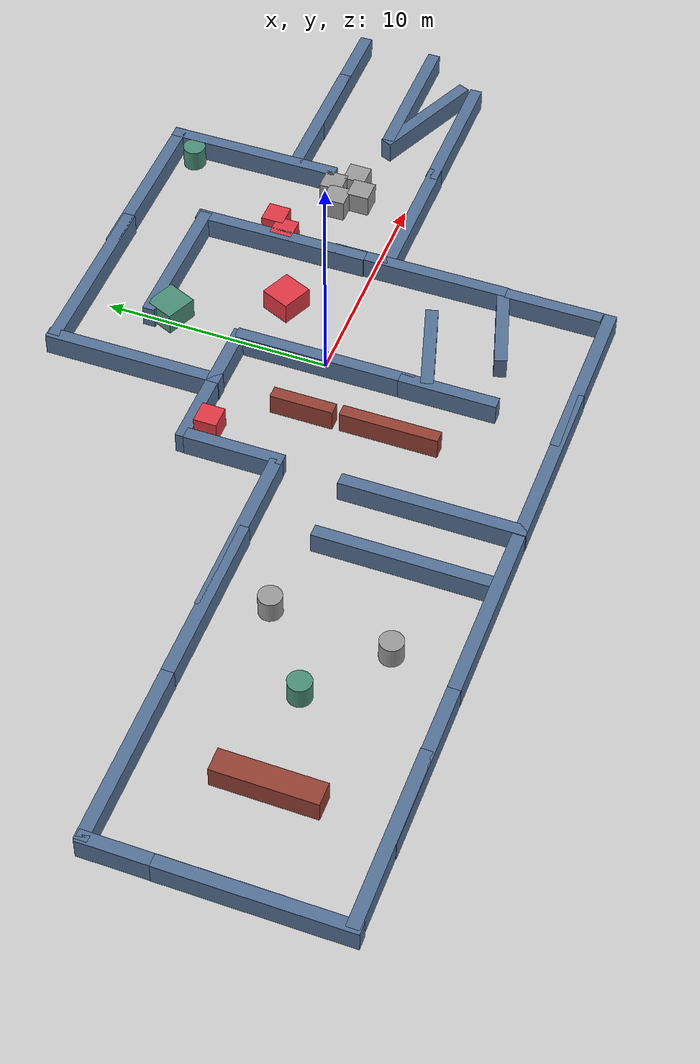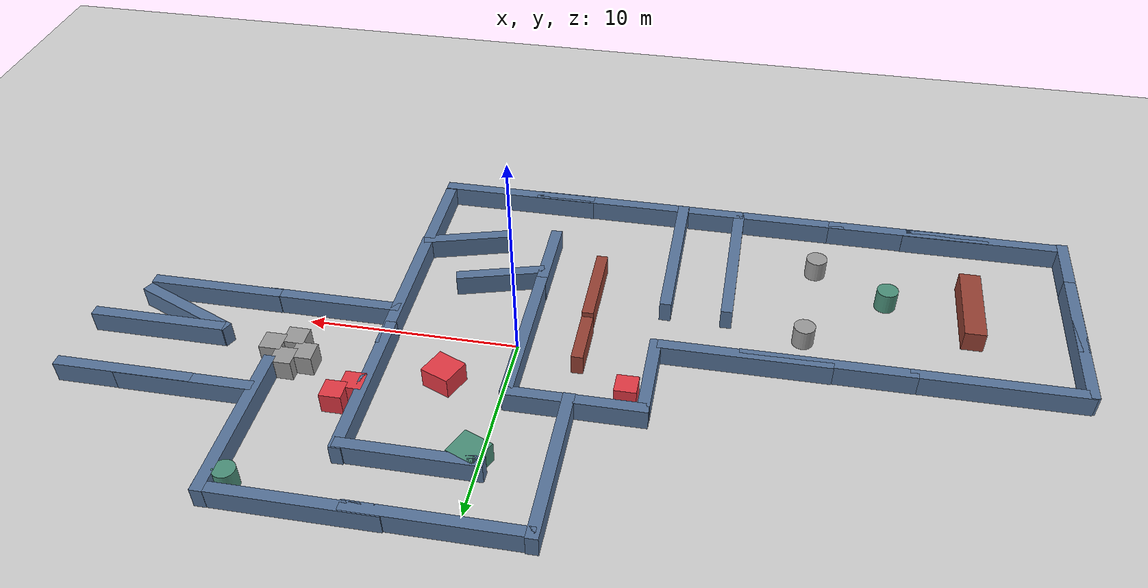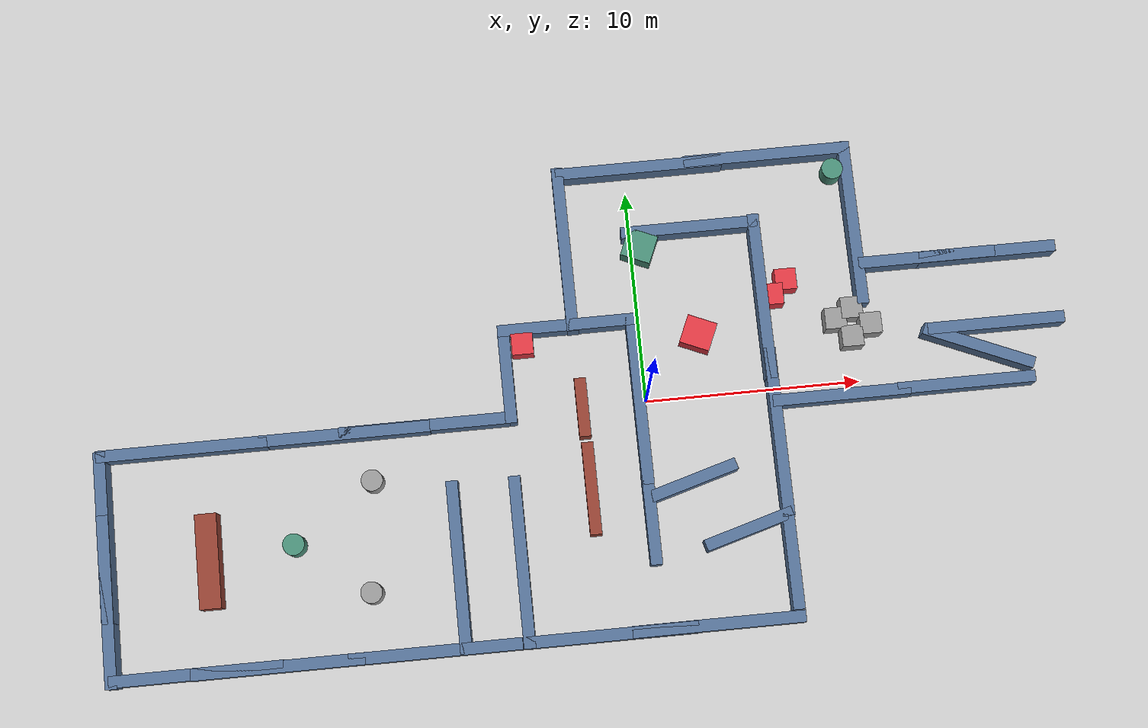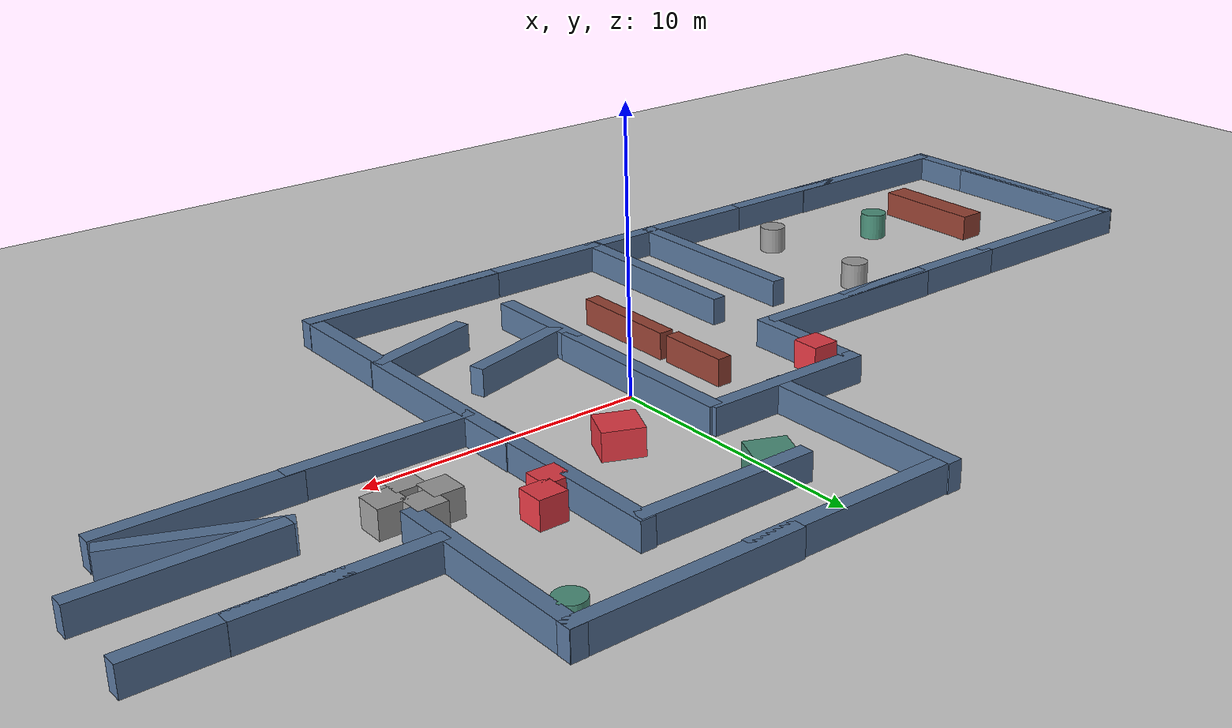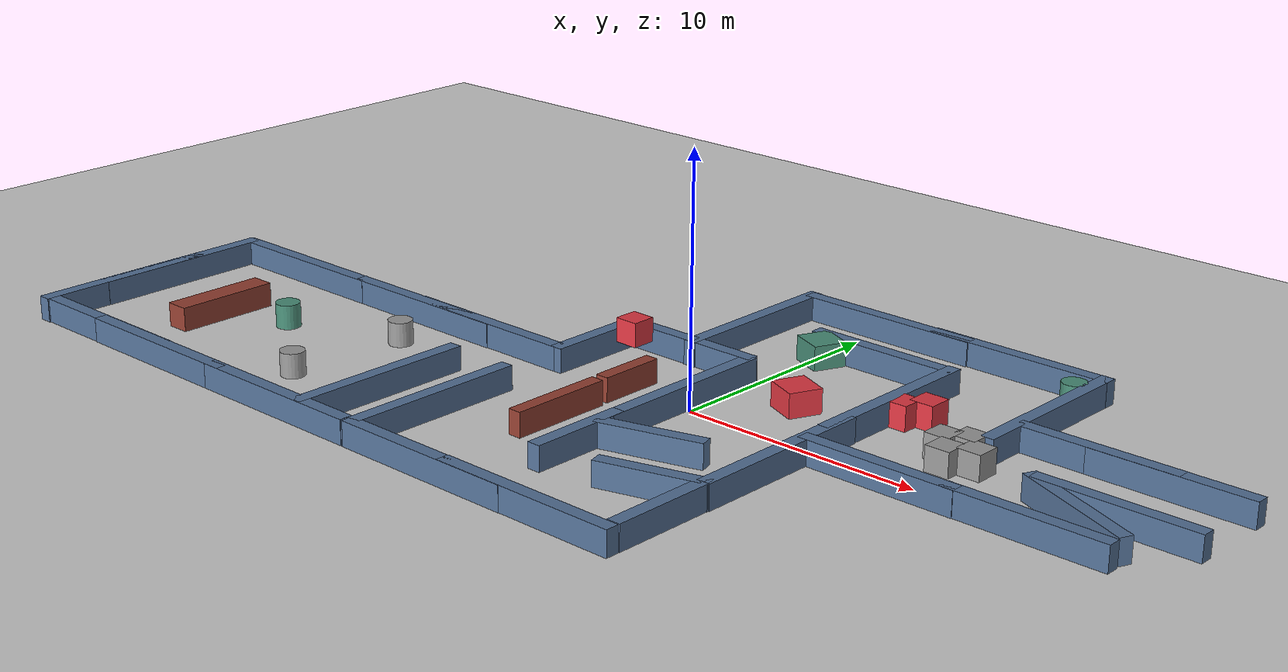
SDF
<sdf version="1.6">
 <world name="default">
  <model name="ground_plane">
   <static>1</static>
   <link name="link">
    <collision name="collision">
     <geometry><plane><normal>0 0 1</normal><size>100 100</size></plane></geometry>
     <surface><friction><ode><mu>100</mu><mu2>50</mu2></ode></friction></surface>
    </collision>
    <visual name="visual">
     <cast_shadows>0</cast_shadows>
     <geometry><plane><normal>0 0 1</normal><size>100 100</size></plane></geometry>
     <material>
      <script><uri>file://media/materials/scripts/gazebo.material</uri><name>Gazebo/Grey</name></script>
     </material>
    </visual>
   </link>
  </model>
  <light name="sun" type="directional">
   <pose>0 0 10 0 -0 0</pose>
   <diffuse>0.8 0.8 0.8 1</diffuse>
   <specular>0.2 0.2 0.2 1</specular>
   <attenuation>
    <range>1000</range>
    <constant>0.9</constant>
    <linear>0.01</linear>
    <quadratic>0.001</quadratic>
   </attenuation>
   <direction>-0.5 0.1 -0.9</direction>
  </light>
  <light name="some_light" type="directional">
   <diffuse>0.7 0.7 0.7 0</diffuse>
   <specular>1 1 1 0</specular>
   <direction>-1 -1 -1</direction>
  </light>
  <model name="mazesummer1">
   <pose>0 -0 0.499991 0 -0 0</pose>
   <link name="box10_link">
    <pose>9.80009 2.02423 9e-06 0 -0 0</pose>
    <inertial>
     <mass>1</mass>
     <inertia>
      <ixx>0.166667</ixx>
      <ixy>0</ixy>
      <ixz>0</ixz>
      <iyy>0.166667</iyy>
      <iyz>0</iyz>
      <izz>0.166667</izz>
     </inertia>
    </inertial>
    <visual name="box10_visual">
     <geometry><box><size>1 1 1</size></box></geometry>
     <material>
      <lighting>1</lighting>
      <script><uri>file://media/materials/scripts/gazebo.material</uri><name>Gazebo/Grey</name></script>
      <ambient>1 1 1 1</ambient>
      <diffuse>1 1 1 1</diffuse>
      <specular>0.01 0.01 0.01 1</specular>
      <emissive>0 0 0 1</emissive>
     </material>
    </visual>
    <collision name="collision">
     <geometry><box><size>1 1 1</size></box></geometry>
     <surface>
      <friction>
       <ode><mu>1</mu><mu2>1</mu2><fdir1>0 0 0</fdir1><slip1>0</slip1><slip2>0</slip2></ode>
       <torsional>
        <coefficient>1</coefficient>
        <patch_radius>0</patch_radius>
        <surface_radius>0</surface_radius>
        <use_patch_radius>1</use_patch_radius>
        <ode><slip>0</slip></ode>
       </torsional>
      </friction>
      <bounce><restitution_coefficient>0</restitution_coefficient><threshold>1e+06</threshold></bounce>
      <contact>
       <collide_without_contact>0</collide_without_contact>
       <collide_without_contact_bitmask>1</collide_without_contact_bitmask>
       <collide_bitmask>1</collide_bitmask>
       <ode>
        <soft_cfm>0</soft_cfm>
        <soft_erp>0.2</soft_erp>
        <kp>1e+13</kp>
        <kd>1</kd>
        <max_vel>0.01</max_vel>
        <min_depth>0</min_depth>
       </ode>
       <bullet>
        <split_impulse>1</split_impulse>
        <split_impulse_penetration_threshold>-0.01</split_impulse_penetration_threshold>
        <soft_cfm>0</soft_cfm>
        <soft_erp>0.2</soft_erp>
        <kp>1e+13</kp>
        <kd>1</kd>
       </bullet>
      </contact>
     </surface>
    </collision>
   </link>
   <link name="cylinder_big_link">
    <pose>-16.6447 -5.27396 0.499997 0 -0 0</pose>
    <inertial>
     <mass>1</mass>
     <inertia><ixx>0.15</ixx><ixy>0</ixy><ixz>0</ixz><iyy>0.15</iyy><iyz>0</iyz><izz>0.13</izz></inertia>
    </inertial>
    <visual name="visual">
     <geometry><cylinder><radius>0.5</radius><length>1</length></cylinder></geometry>
     <material>
      <lighting>1</lighting>
      <script><uri>file://media/materials/scripts/gazebo.material</uri><name>Gazebo/Grey</name></script>
      <ambient>0.290196 0.560784 0.47451 1</ambient>
      <diffuse>0.290196 0.560784 0.47451 1</diffuse>
      <specular>0.01 0.01 0.01 1</specular>
      <emissive>0 0 0 1</emissive>
     </material>
    </visual>
    <collision name="collision">
     <geometry><cylinder><radius>0.5</radius><length>1</length></cylinder></geometry>
     <surface>
      <friction>
       <ode><mu>1</mu><mu2>1</mu2><fdir1>0 0 0</fdir1><slip1>0</slip1><slip2>0</slip2></ode>
       <torsional>
        <coefficient>1</coefficient>
        <patch_radius>0</patch_radius>
        <surface_radius>0</surface_radius>
        <use_patch_radius>1</use_patch_radius>
        <ode><slip>0</slip></ode>
       </torsional>
      </friction>
      <bounce><restitution_coefficient>0</restitution_coefficient><threshold>1e+06</threshold></bounce>
      <contact>
       <collide_without_contact>0</collide_without_contact>
       <collide_without_contact_bitmask>1</collide_without_contact_bitmask>
       <collide_bitmask>1</collide_bitmask>
       <ode>
        <soft_cfm>0</soft_cfm>
        <soft_erp>0.2</soft_erp>
        <kp>1e+13</kp>
        <kd>1</kd>
        <max_vel>0.01</max_vel>
        <min_depth>0</min_depth>
       </ode>
       <bullet>
        <split_impulse>1</split_impulse>
        <split_impulse_penetration_threshold>-0.01</split_impulse_penetration_threshold>
        <soft_cfm>0</soft_cfm>
        <soft_erp>0.2</soft_erp>
        <kp>1e+13</kp>
        <kd>1</kd>
       </bullet>
      </contact>
     </surface>
    </collision>
   </link>
   <link name="wall1_custom_link">
    <pose>-20.6541 -5.60724 -0.000514 -0.000514 -6e-06 0</pose>
    <inertial>
     <mass>2.3361</mass>
     <inertia><ixx>0.25269</ixx><ixy>0</ixy><ixz>0</ixz><iyy>3.75965</iyy><iyz>0</iyz><izz>3.62299</izz></inertia>
    </inertial>
    <visual name="visual">
     <geometry><box><size>1 4.35376 1</size></box></geometry>
     <material>
      <lighting>1</lighting>
      <script><uri>file://media/materials/scripts/gazebo.material</uri><name>Gazebo/Grey</name></script>
      <ambient>0.580392 0.25098 0.196078 1</ambient>
      <diffuse>0.580392 0.25098 0.196078 1</diffuse>
      <specular>0.01 0.01 0.01 1</specular>
      <emissive>0 0 0 1</emissive>
      <shader type="pixel"/>
     </material>
    </visual>
    <collision name="collision">
     <geometry><box><size>1 4.35376 1</size></box></geometry>
     <surface>
      <friction>
       <ode><mu>1</mu><mu2>1</mu2><fdir1>0 0 0</fdir1><slip1>0</slip1><slip2>0</slip2></ode>
       <torsional>
        <coefficient>1</coefficient>
        <patch_radius>0</patch_radius>
        <surface_radius>0</surface_radius>
        <use_patch_radius>1</use_patch_radius>
        <ode><slip>0</slip></ode>
       </torsional>
      </friction>
      <bounce><restitution_coefficient>0</restitution_coefficient><threshold>1e+06</threshold></bounce>
      <contact>
       <collide_without_contact>0</collide_without_contact>
       <collide_without_contact_bitmask>1</collide_without_contact_bitmask>
       <collide_bitmask>1</collide_bitmask>
       <ode>
        <soft_cfm>0</soft_cfm>
        <soft_erp>0.2</soft_erp>
        <kp>1e+13</kp>
        <kd>1</kd>
        <max_vel>0.01</max_vel>
        <min_depth>0</min_depth>
       </ode>
       <bullet>
        <split_impulse>1</split_impulse>
        <split_impulse_penetration_threshold>-0.01</split_impulse_penetration_threshold>
        <soft_cfm>0</soft_cfm>
        <soft_erp>0.2</soft_erp>
        <kp>1e+13</kp>
        <kd>1</kd>
       </bullet>
      </contact>
     </surface>
    </collision>
   </link>
   <link name="link_11">
    <pose>6.31823 4.34711 9e-06 0 -0 0</pose>
    <inertial>
     <mass>1</mass>
     <inertia>
      <ixx>0.166667</ixx>
      <ixy>0</ixy>
      <ixz>0</ixz>
      <iyy>0.166667</iyy>
      <iyz>0</iyz>
      <izz>0.166667</izz>
     </inertia>
    </inertial>
    <visual name="visual">
     <geometry><box><size>1 1 1</size></box></geometry>
     <material>
      <lighting>1</lighting>
      <script><uri>file://media/materials/scripts/gazebo.material</uri><name>Gazebo/Grey</name></script>
      <ambient>0.882353 0.219608 0.262745 1</ambient>
      <diffuse>0.882353 0.219608 0.262745 1</diffuse>
      <specular>0.01 0.01 0.01 1</specular>
      <emissive>0 0 0 1</emissive>
     </material>
    </visual>
    <collision name="collision">
     <geometry><box><size>1 1 1</size></box></geometry>
     <surface>
      <friction>
       <ode><mu>1</mu><mu2>1</mu2><fdir1>0 0 0</fdir1><slip1>0</slip1><slip2>0</slip2></ode>
       <torsional>
        <coefficient>1</coefficient>
        <patch_radius>0</patch_radius>
        <surface_radius>0</surface_radius>
        <use_patch_radius>1</use_patch_radius>
        <ode><slip>0</slip></ode>
       </torsional>
      </friction>
      <bounce><restitution_coefficient>0</restitution_coefficient><threshold>1e+06</threshold></bounce>
      <contact>
       <collide_without_contact>0</collide_without_contact>
       <collide_without_contact_bitmask>1</collide_without_contact_bitmask>
       <collide_bitmask>1</collide_bitmask>
       <ode>
        <soft_cfm>0</soft_cfm>
        <soft_erp>0.2</soft_erp>
        <kp>1e+13</kp>
        <kd>1</kd>
        <max_vel>0.01</max_vel>
        <min_depth>0</min_depth>
       </ode>
       <bullet>
        <split_impulse>1</split_impulse>
        <split_impulse_penetration_threshold>-0.01</split_impulse_penetration_threshold>
        <soft_cfm>0</soft_cfm>
        <soft_erp>0.2</soft_erp>
        <kp>1e+13</kp>
        <kd>1</kd>
       </bullet>
      </contact>
     </surface>
    </collision>
   </link>
   <link name="link_12">
    <pose>7.00494 5.00129 9e-06 0 -0 0</pose>
    <inertial>
     <mass>1</mass>
     <inertia>
      <ixx>0.166667</ixx>
      <ixy>0</ixy>
      <ixz>0</ixz>
      <iyy>0.166667</iyy>
      <iyz>0</iyz>
      <izz>0.166667</izz>
     </inertia>
    </inertial>
    <visual name="visual">
     <geometry><box><size>1 1 1</size></box></geometry>
     <material>
      <lighting>1</lighting>
      <script><uri>file://media/materials/scripts/gazebo.material</uri><name>Gazebo/Grey</name></script>
      <ambient>0.882353 0.219608 0.262745 1</ambient>
      <diffuse>0.882353 0.219608 0.262745 1</diffuse>
      <specular>0.01 0.01 0.01 1</specular>
      <emissive>0 0 0 1</emissive>
     </material>
    </visual>
    <collision name="collision">
     <geometry><box><size>1 1 1</size></box></geometry>
     <surface>
      <friction>
       <ode><mu>1</mu><mu2>1</mu2><fdir1>0 0 0</fdir1><slip1>0</slip1><slip2>0</slip2></ode>
       <torsional>
        <coefficient>1</coefficient>
        <patch_radius>0</patch_radius>
        <surface_radius>0</surface_radius>
        <use_patch_radius>1</use_patch_radius>
        <ode><slip>0</slip></ode>
       </torsional>
      </friction>
      <bounce><restitution_coefficient>0</restitution_coefficient><threshold>1e+06</threshold></bounce>
      <contact>
       <collide_without_contact>0</collide_without_contact>
       <collide_without_contact_bitmask>1</collide_without_contact_bitmask>
       <collide_bitmask>1</collide_bitmask>
       <ode>
        <soft_cfm>0</soft_cfm>
        <soft_erp>0.2</soft_erp>
        <kp>1e+13</kp>
        <kd>1</kd>
        <max_vel>0.01</max_vel>
        <min_depth>0</min_depth>
       </ode>
       <bullet>
        <split_impulse>1</split_impulse>
        <split_impulse_penetration_threshold>-0.01</split_impulse_penetration_threshold>
        <soft_cfm>0</soft_cfm>
        <soft_erp>0.2</soft_erp>
        <kp>1e+13</kp>
        <kd>1</kd>
       </bullet>
      </contact>
     </surface>
    </collision>
   </link>
   <link name="maze2_box">
    <pose>-5.520520 2.979450 0.5 0 -0 0</pose>
    <inertial>
     <mass>1</mass>
     <inertia>
      <ixx>0.166667</ixx>
      <ixy>0</ixy>
      <ixz>0</ixz>
      <iyy>0.166667</iyy>
      <iyz>0</iyz>
      <izz>0.166667</izz>
     </inertia>
    </inertial>
    <visual name="visual">
     <geometry><box><size>1 1 1</size></box></geometry>
     <material>
      <lighting>1</lighting>
      <script><uri>file://media/materials/scripts/gazebo.material</uri><name>Gazebo/Grey</name></script>
      <ambient>0.882353 0.219608 0.262745 1</ambient>
      <diffuse>0.882353 0.219608 0.262745 1</diffuse>
      <specular>0.01 0.01 0.01 1</specular>
      <emissive>0 0 0 1</emissive>
     </material>
    </visual>
    <collision name="collision">
     <geometry><box><size>1 1 1</size></box></geometry>
     <surface>
      <friction>
       <ode><mu>1</mu><mu2>1</mu2><fdir1>0 0 0</fdir1><slip1>0</slip1><slip2>0</slip2></ode>
       <torsional>
        <coefficient>1</coefficient>
        <patch_radius>0</patch_radius>
        <surface_radius>0</surface_radius>
        <use_patch_radius>1</use_patch_radius>
        <ode><slip>0</slip></ode>
       </torsional>
      </friction>
      <bounce><restitution_coefficient>0</restitution_coefficient><threshold>1e+06</threshold></bounce>
      <contact>
       <collide_without_contact>0</collide_without_contact>
       <collide_without_contact_bitmask>1</collide_without_contact_bitmask>
       <collide_bitmask>1</collide_bitmask>
       <ode>
        <soft_cfm>0</soft_cfm>
        <soft_erp>0.2</soft_erp>
        <kp>1e+13</kp>
        <kd>1</kd>
        <max_vel>0.01</max_vel>
        <min_depth>0</min_depth>
       </ode>
       <bullet>
        <split_impulse>1</split_impulse>
        <split_impulse_penetration_threshold>-0.01</split_impulse_penetration_threshold>
        <soft_cfm>0</soft_cfm>
        <soft_erp>0.2</soft_erp>
        <kp>1e+13</kp>
        <kd>1</kd>
       </bullet>
      </contact>
     </surface>
    </collision>
   </link>
   <link name="box9_link">
    <pose>10.7124 2.54643 9e-06 0 -0 0</pose>
    <inertial>
     <mass>1</mass>
     <inertia>
      <ixx>0.166667</ixx>
      <ixy>0</ixy>
      <ixz>0</ixz>
      <iyy>0.166667</iyy>
      <iyz>0</iyz>
      <izz>0.166667</izz>
     </inertia>
    </inertial>
    <visual name="box9_visual">
     <geometry><box><size>1 1 1</size></box></geometry>
     <material>
      <lighting>1</lighting>
      <script><uri>file://media/materials/scripts/gazebo.material</uri><name>Gazebo/Grey</name></script>
      <ambient>1 1 1 1</ambient>
      <diffuse>1 1 1 1</diffuse>
      <specular>0.01 0.01 0.01 1</specular>
      <emissive>0 0 0 1</emissive>
     </material>
    </visual>
    <collision name="collision">
     <geometry><box><size>1 1 1</size></box></geometry>
     <surface>
      <friction>
       <ode><mu>1</mu><mu2>1</mu2><fdir1>0 0 0</fdir1><slip1>0</slip1><slip2>0</slip2></ode>
       <torsional>
        <coefficient>1</coefficient>
        <patch_radius>0</patch_radius>
        <surface_radius>0</surface_radius>
        <use_patch_radius>1</use_patch_radius>
        <ode><slip>0</slip></ode>
       </torsional>
      </friction>
      <bounce><restitution_coefficient>0</restitution_coefficient><threshold>1e+06</threshold></bounce>
      <contact>
       <collide_without_contact>0</collide_without_contact>
       <collide_without_contact_bitmask>1</collide_without_contact_bitmask>
       <collide_bitmask>1</collide_bitmask>
       <ode>
        <soft_cfm>0</soft_cfm>
        <soft_erp>0.2</soft_erp>
        <kp>1e+13</kp>
        <kd>1</kd>
        <max_vel>0.01</max_vel>
        <min_depth>0</min_depth>
       </ode>
       <bullet>
        <split_impulse>1</split_impulse>
        <split_impulse_penetration_threshold>-0.01</split_impulse_penetration_threshold>
        <soft_cfm>0</soft_cfm>
        <soft_erp>0.2</soft_erp>
        <kp>1e+13</kp>
        <kd>1</kd>
       </bullet>
      </contact>
     </surface>
    </collision>
   </link>
   <link name="wall0_link">
    <pose>-21.4897 -10.6297 9e-06 0 -0 0</pose>
    <inertial>
     <mass>4.30693</mass>
     <inertia><ixx>0.46587</ixx><ixy>0</ixy><ixz>0</ixz><iyy>22.6991</iyy><iyz>0</iyz><izz>22.4471</izz></inertia>
    </inertial>
    <visual name="visual">
     <geometry><box><size>7.88951 0.545905 1</size></box></geometry>
     <material>
      <lighting>1</lighting>
      <script><uri>file://media/materials/scripts/gazebo.material</uri><name>Gazebo/Grey</name></script>
      <ambient>0.333333 0.447059 0.592157 1</ambient>
      <diffuse>0.333333 0.447059 0.592157 1</diffuse>
      <specular>0.01 0.01 0.01 1</specular>
      <emissive>0 0 0 1</emissive>
      <shader type="pixel"/>
     </material>
    </visual>
    <collision name="collision">
     <geometry><box><size>7.88951 0.545905 1</size></box></geometry>
     <surface>
      <friction>
       <ode><mu>1</mu><mu2>1</mu2><fdir1>0 0 0</fdir1><slip1>0</slip1><slip2>0</slip2></ode>
       <torsional>
        <coefficient>1</coefficient>
        <patch_radius>0</patch_radius>
        <surface_radius>0</surface_radius>
        <use_patch_radius>1</use_patch_radius>
        <ode><slip>0</slip></ode>
       </torsional>
      </friction>
      <bounce><restitution_coefficient>0</restitution_coefficient><threshold>1e+06</threshold></bounce>
      <contact>
       <collide_without_contact>0</collide_without_contact>
       <collide_without_contact_bitmask>1</collide_without_contact_bitmask>
       <collide_bitmask>1</collide_bitmask>
       <ode>
        <soft_cfm>0</soft_cfm>
        <soft_erp>0.2</soft_erp>
        <kp>1e+13</kp>
        <kd>1</kd>
        <max_vel>0.01</max_vel>
        <min_depth>0</min_depth>
       </ode>
       <bullet>
        <split_impulse>1</split_impulse>
        <split_impulse_penetration_threshold>-0.01</split_impulse_penetration_threshold>
        <soft_cfm>0</soft_cfm>
        <soft_erp>0.2</soft_erp>
        <kp>1e+13</kp>
        <kd>1</kd>
       </bullet>
      </contact>
     </surface>
    </collision>
   </link>
   <link name="wall1_link">
    <pose>-17.8012 -10.6509 9e-06 0 -0 0</pose>
    <inertial>
     <mass>4.30693</mass>
     <inertia><ixx>0.46587</ixx><ixy>0</ixy><ixz>0</ixz><iyy>22.6991</iyy><iyz>0</iyz><izz>22.4471</izz></inertia>
    </inertial>
    <visual name="visual">
     <geometry><box><size>7.88951 0.545905 1</size></box></geometry>
     <material>
      <lighting>1</lighting>
      <script><uri>file://media/materials/scripts/gazebo.material</uri><name>Gazebo/Grey</name></script>
      <ambient>0.333333 0.447059 0.592157 1</ambient>
      <diffuse>0.333333 0.447059 0.592157 1</diffuse>
      <specular>0.01 0.01 0.01 1</specular>
      <emissive>0 0 0 1</emissive>
      <shader type="pixel"/>
     </material>
    </visual>
    <collision name="collision">
     <geometry><box><size>7.88951 0.545905 1</size></box></geometry>
     <surface>
      <friction>
       <ode><mu>1</mu><mu2>1</mu2><fdir1>0 0 0</fdir1><slip1>0</slip1><slip2>0</slip2></ode>
       <torsional>
        <coefficient>1</coefficient>
        <patch_radius>0</patch_radius>
        <surface_radius>0</surface_radius>
        <use_patch_radius>1</use_patch_radius>
        <ode><slip>0</slip></ode>
       </torsional>
      </friction>
      <bounce><restitution_coefficient>0</restitution_coefficient><threshold>1e+06</threshold></bounce>
      <contact>
       <collide_without_contact>0</collide_without_contact>
       <collide_without_contact_bitmask>1</collide_without_contact_bitmask>
       <collide_bitmask>1</collide_bitmask>
       <ode>
        <soft_cfm>0</soft_cfm>
        <soft_erp>0.2</soft_erp>
        <kp>1e+13</kp>
        <kd>1</kd>
        <max_vel>0.01</max_vel>
        <min_depth>0</min_depth>
       </ode>
       <bullet>
        <split_impulse>1</split_impulse>
        <split_impulse_penetration_threshold>-0.01</split_impulse_penetration_threshold>
        <soft_cfm>0</soft_cfm>
        <soft_erp>0.2</soft_erp>
        <kp>1e+13</kp>
        <kd>1</kd>
       </bullet>
      </contact>
     </surface>
    </collision>
   </link>
   <link name="wall20_link">
    <pose>-21.5718 -0.350427 9e-06 0 -0 0</pose>
    <inertial>
     <mass>4.30693</mass>
     <inertia><ixx>0.46587</ixx><ixy>0</ixy><ixz>0</ixz><iyy>22.6991</iyy><iyz>0</iyz><izz>22.4471</izz></inertia>
    </inertial>
    <visual name="visual">
     <geometry><box><size>7.88951 0.545905 1</size></box></geometry>
     <material>
      <lighting>1</lighting>
      <script><uri>file://media/materials/scripts/gazebo.material</uri><name>Gazebo/Grey</name></script>
      <ambient>0.333333 0.447059 0.592157 1</ambient>
      <diffuse>0.333333 0.447059 0.592157 1</diffuse>
      <specular>0.01 0.01 0.01 1</specular>
      <emissive>0 0 0 1</emissive>
      <shader type="pixel"/>
     </material>
    </visual>
    <collision name="collision">
     <geometry><box><size>7.88951 0.545905 1</size></box></geometry>
     <surface>
      <friction>
       <ode><mu>1</mu><mu2>1</mu2><fdir1>0 0 0</fdir1><slip1>0</slip1><slip2>0</slip2></ode>
       <torsional>
        <coefficient>1</coefficient>
        <patch_radius>0</patch_radius>
        <surface_radius>0</surface_radius>
        <use_patch_radius>1</use_patch_radius>
        <ode><slip>0</slip></ode>
       </torsional>
      </friction>
      <bounce><restitution_coefficient>0</restitution_coefficient><threshold>1e+06</threshold></bounce>
      <contact>
       <collide_without_contact>0</collide_without_contact>
       <collide_without_contact_bitmask>1</collide_without_contact_bitmask>
       <collide_bitmask>1</collide_bitmask>
       <ode>
        <soft_cfm>0</soft_cfm>
        <soft_erp>0.2</soft_erp>
        <kp>1e+13</kp>
        <kd>1</kd>
        <max_vel>0.01</max_vel>
        <min_depth>0</min_depth>
       </ode>
       <bullet>
        <split_impulse>1</split_impulse>
        <split_impulse_penetration_threshold>-0.01</split_impulse_penetration_threshold>
        <soft_cfm>0</soft_cfm>
        <soft_erp>0.2</soft_erp>
        <kp>1e+13</kp>
        <kd>1</kd>
       </bullet>
      </contact>
     </surface>
    </collision>
   </link>
   <link name="wall21_link">
    <pose>-14.0594 -0.346312 9e-06 0 -0 0</pose>
    <inertial>
     <mass>4.30693</mass>
     <inertia><ixx>0.46587</ixx><ixy>0</ixy><ixz>0</ixz><iyy>22.6991</iyy><iyz>0</iyz><izz>22.4471</izz></inertia>
    </inertial>
    <visual name="visual">
     <geometry><box><size>7.88951 0.545905 1</size></box></geometry>
     <material>
      <lighting>1</lighting>
      <script><uri>file://media/materials/scripts/gazebo.material</uri><name>Gazebo/Grey</name></script>
      <ambient>0.333333 0.447059 0.592157 1</ambient>
      <diffuse>0.333333 0.447059 0.592157 1</diffuse>
      <specular>0.01 0.01 0.01 1</specular>
      <emissive>0 0 0 1</emissive>
      <shader type="pixel"/>
     </material>
    </visual>
    <collision name="collision">
     <geometry><box><size>7.88951 0.545905 1</size></box></geometry>
     <surface>
      <friction>
       <ode><mu>1</mu><mu2>1</mu2><fdir1>0 0 0</fdir1><slip1>0</slip1><slip2>0</slip2></ode>
       <torsional>
        <coefficient>1</coefficient>
        <patch_radius>0</patch_radius>
        <surface_radius>0</surface_radius>
        <use_patch_radius>1</use_patch_radius>
        <ode><slip>0</slip></ode>
       </torsional>
      </friction>
      <bounce><restitution_coefficient>0</restitution_coefficient><threshold>1e+06</threshold></bounce>
      <contact>
       <collide_without_contact>0</collide_without_contact>
       <collide_without_contact_bitmask>1</collide_without_contact_bitmask>
       <collide_bitmask>1</collide_bitmask>
       <ode>
        <soft_cfm>0</soft_cfm>
        <soft_erp>0.2</soft_erp>
        <kp>1e+13</kp>
        <kd>1</kd>
        <max_vel>0.01</max_vel>
        <min_depth>0</min_depth>
       </ode>
       <bullet>
        <split_impulse>1</split_impulse>
        <split_impulse_penetration_threshold>-0.01</split_impulse_penetration_threshold>
        <soft_cfm>0</soft_cfm>
        <soft_erp>0.2</soft_erp>
        <kp>1e+13</kp>
        <kd>1</kd>
       </bullet>
      </contact>
     </surface>
    </collision>
   </link>
   <link name="wall3_link">
    <pose>-10.6658 -10.6545 9e-06 0 -0 0</pose>
    <inertial>
     <mass>4.30693</mass>
     <inertia><ixx>0.46587</ixx><ixy>0</ixy><ixz>0</ixz><iyy>22.6991</iyy><iyz>0</iyz><izz>22.4471</izz></inertia>
    </inertial>
    <visual name="visual">
     <geometry><box><size>7.88951 0.545905 1</size></box></geometry>
     <material>
      <lighting>1</lighting>
      <script><uri>file://media/materials/scripts/gazebo.material</uri><name>Gazebo/Grey</name></script>
      <ambient>0.333333 0.447059 0.592157 1</ambient>
      <diffuse>0.333333 0.447059 0.592157 1</diffuse>
      <specular>0.01 0.01 0.01 1</specular>
      <emissive>0 0 0 1</emissive>
      <shader type="pixel"/>
     </material>
    </visual>
    <collision name="collision">
     <geometry><box><size>7.88951 0.545905 1</size></box></geometry>
     <surface>
      <friction>
       <ode><mu>1</mu><mu2>1</mu2><fdir1>0 0 0</fdir1><slip1>0</slip1><slip2>0</slip2></ode>
       <torsional>
        <coefficient>1</coefficient>
        <patch_radius>0</patch_radius>
        <surface_radius>0</surface_radius>
        <use_patch_radius>1</use_patch_radius>
        <ode><slip>0</slip></ode>
       </torsional>
      </friction>
      <bounce><restitution_coefficient>0</restitution_coefficient><threshold>1e+06</threshold></bounce>
      <contact>
       <collide_without_contact>0</collide_without_contact>
       <collide_without_contact_bitmask>1</collide_without_contact_bitmask>
       <collide_bitmask>1</collide_bitmask>
       <ode>
        <soft_cfm>0</soft_cfm>
        <soft_erp>0.2</soft_erp>
        <kp>1e+13</kp>
        <kd>1</kd>
        <max_vel>0.01</max_vel>
        <min_depth>0</min_depth>
       </ode>
       <bullet>
        <split_impulse>1</split_impulse>
        <split_impulse_penetration_threshold>-0.01</split_impulse_penetration_threshold>
        <soft_cfm>0</soft_cfm>
        <soft_erp>0.2</soft_erp>
        <kp>1e+13</kp>
        <kd>1</kd>
       </bullet>
      </contact>
     </surface>
    </collision>
   </link>
   <link name="wall24_link">
    <pose>-3.41756 3.78222 9e-06 0 -0 0</pose>
    <inertial>
     <mass>3.50538</mass>
     <inertia><ixx>0.379168</ixx><ixy>0</ixy><ixz>0</ixz><iyy>12.3366</iyy><iyz>0</iyz><izz>12.1315</izz></inertia>
    </inertial>
    <visual name="visual">
     <geometry><box><size>6.42122 0.545905 1</size></box></geometry>
     <material>
      <lighting>1</lighting>
      <script><uri>file://media/materials/scripts/gazebo.material</uri><name>Gazebo/Grey</name></script>
      <ambient>0.333333 0.447059 0.592157 1</ambient>
      <diffuse>0.333333 0.447059 0.592157 1</diffuse>
      <specular>0.01 0.01 0.01 1</specular>
      <emissive>0 0 0 1</emissive>
      <shader type="pixel"/>
     </material>
    </visual>
    <collision name="collision">
     <geometry><box><size>6.42122 0.545905 1</size></box></geometry>
     <surface>
      <friction>
       <ode><mu>1</mu><mu2>1</mu2><fdir1>0 0 0</fdir1><slip1>0</slip1><slip2>0</slip2></ode>
       <torsional>
        <coefficient>1</coefficient>
        <patch_radius>0</patch_radius>
        <surface_radius>0</surface_radius>
        <use_patch_radius>1</use_patch_radius>
        <ode><slip>0</slip></ode>
       </torsional>
      </friction>
      <bounce><restitution_coefficient>0</restitution_coefficient><threshold>1e+06</threshold></bounce>
      <contact>
       <collide_without_contact>0</collide_without_contact>
       <collide_without_contact_bitmask>1</collide_without_contact_bitmask>
       <collide_bitmask>1</collide_bitmask>
       <ode>
        <soft_cfm>0</soft_cfm>
        <soft_erp>0.2</soft_erp>
        <kp>1e+13</kp>
        <kd>1</kd>
        <max_vel>0.01</max_vel>
        <min_depth>0</min_depth>
       </ode>
       <bullet>
        <split_impulse>1</split_impulse>
        <split_impulse_penetration_threshold>-0.01</split_impulse_penetration_threshold>
        <soft_cfm>0</soft_cfm>
        <soft_erp>0.2</soft_erp>
        <kp>1e+13</kp>
        <kd>1</kd>
       </bullet>
      </contact>
     </surface>
    </collision>
   </link>
   <link name="wall7_link">
    <pose>-2.67814 -10.6624 9e-06 0 -0 0</pose>
    <inertial>
     <mass>4.30693</mass>
     <inertia><ixx>0.46587</ixx><ixy>0</ixy><ixz>0</ixz><iyy>22.6991</iyy><iyz>0</iyz><izz>22.4471</izz></inertia>
    </inertial>
    <visual name="visual">
     <geometry><box><size>7.88951 0.545905 1</size></box></geometry>
     <material>
      <lighting>1</lighting>
      <script><uri>file://media/materials/scripts/gazebo.material</uri><name>Gazebo/Grey</name></script>
      <ambient>0.333333 0.447059 0.592157 1</ambient>
      <diffuse>0.333333 0.447059 0.592157 1</diffuse>
      <specular>0.01 0.01 0.01 1</specular>
      <emissive>0 0 0 1</emissive>
      <shader type="pixel"/>
     </material>
    </visual>
    <collision name="collision">
     <geometry><box><size>7.88951 0.545905 1</size></box></geometry>
     <surface>
      <friction>
       <ode><mu>1</mu><mu2>1</mu2><fdir1>0 0 0</fdir1><slip1>0</slip1><slip2>0</slip2></ode>
       <torsional>
        <coefficient>1</coefficient>
        <patch_radius>0</patch_radius>
        <surface_radius>0</surface_radius>
        <use_patch_radius>1</use_patch_radius>
        <ode><slip>0</slip></ode>
       </torsional>
      </friction>
      <bounce><restitution_coefficient>0</restitution_coefficient><threshold>1e+06</threshold></bounce>
      <contact>
       <collide_without_contact>0</collide_without_contact>
       <collide_without_contact_bitmask>1</collide_without_contact_bitmask>
       <collide_bitmask>1</collide_bitmask>
       <ode>
        <soft_cfm>0</soft_cfm>
        <soft_erp>0.2</soft_erp>
        <kp>1e+13</kp>
        <kd>1</kd>
        <max_vel>0.01</max_vel>
        <min_depth>0</min_depth>
       </ode>
       <bullet>
        <split_impulse>1</split_impulse>
        <split_impulse_penetration_threshold>-0.01</split_impulse_penetration_threshold>
        <soft_cfm>0</soft_cfm>
        <soft_erp>0.2</soft_erp>
        <kp>1e+13</kp>
        <kd>1</kd>
       </bullet>
      </contact>
     </surface>
    </collision>
   </link>
   <link name="wall8_link">
    <pose>2.19804 -10.643 9e-06 0 -0 0</pose>
    <inertial>
     <mass>4.30693</mass>
     <inertia><ixx>0.46587</ixx><ixy>0</ixy><ixz>0</ixz><iyy>22.6991</iyy><iyz>0</iyz><izz>22.4471</izz></inertia>
    </inertial>
    <visual name="visual">
     <geometry><box><size>7.88951 0.545905 1</size></box></geometry>
     <material>
      <lighting>1</lighting>
      <script><uri>file://media/materials/scripts/gazebo.material</uri><name>Gazebo/Grey</name></script>
      <ambient>0.333333 0.447059 0.592157 1</ambient>
      <diffuse>0.333333 0.447059 0.592157 1</diffuse>
      <specular>0.01 0.01 0.01 1</specular>
      <emissive>0 0 0 1</emissive>
      <shader type="pixel"/>
     </material>
    </visual>
    <collision name="collision">
     <geometry><box><size>7.88951 0.545905 1</size></box></geometry>
     <surface>
      <friction>
       <ode><mu>1</mu><mu2>1</mu2><fdir1>0 0 0</fdir1><slip1>0</slip1><slip2>0</slip2></ode>
       <torsional>
        <coefficient>1</coefficient>
        <patch_radius>0</patch_radius>
        <surface_radius>0</surface_radius>
        <use_patch_radius>1</use_patch_radius>
        <ode><slip>0</slip></ode>
       </torsional>
      </friction>
      <bounce><restitution_coefficient>0</restitution_coefficient><threshold>1e+06</threshold></bounce>
      <contact>
       <collide_without_contact>0</collide_without_contact>
       <collide_without_contact_bitmask>1</collide_without_contact_bitmask>
       <collide_bitmask>1</collide_bitmask>
       <ode>
        <soft_cfm>0</soft_cfm>
        <soft_erp>0.2</soft_erp>
        <kp>1e+13</kp>
        <kd>1</kd>
        <max_vel>0.01</max_vel>
        <min_depth>0</min_depth>
       </ode>
       <bullet>
        <split_impulse>1</split_impulse>
        <split_impulse_penetration_threshold>-0.01</split_impulse_penetration_threshold>
        <soft_cfm>0</soft_cfm>
        <soft_erp>0.2</soft_erp>
        <kp>1e+13</kp>
        <kd>1</kd>
       </bullet>
      </contact>
     </surface>
    </collision>
   </link>
   <link name="wall31_link">
    <pose>0.695253 11.0512 9e-06 0 -0 0</pose>
    <inertial>
     <mass>4.30693</mass>
     <inertia><ixx>0.46587</ixx><ixy>0</ixy><ixz>0</ixz><iyy>22.6991</iyy><iyz>0</iyz><izz>22.4471</izz></inertia>
    </inertial>
    <visual name="visual">
     <geometry><box><size>7.88951 0.545905 1</size></box></geometry>
     <material>
      <lighting>1</lighting>
      <script><uri>file://media/materials/scripts/gazebo.material</uri><name>Gazebo/Grey</name></script>
      <ambient>0.333333 0.447059 0.592157 1</ambient>
      <diffuse>0.333333 0.447059 0.592157 1</diffuse>
      <specular>0.01 0.01 0.01 1</specular>
      <emissive>0 0 0 1</emissive>
      <shader type="pixel"/>
     </material>
    </visual>
    <collision name="collision">
     <geometry><box><size>7.88951 0.545905 1</size></box></geometry>
     <surface>
      <friction>
       <ode><mu>1</mu><mu2>1</mu2><fdir1>0 0 0</fdir1><slip1>0</slip1><slip2>0</slip2></ode>
       <torsional>
        <coefficient>1</coefficient>
        <patch_radius>0</patch_radius>
        <surface_radius>0</surface_radius>
        <use_patch_radius>1</use_patch_radius>
        <ode><slip>0</slip></ode>
       </torsional>
      </friction>
      <bounce><restitution_coefficient>0</restitution_coefficient><threshold>1e+06</threshold></bounce>
      <contact>
       <collide_without_contact>0</collide_without_contact>
       <collide_without_contact_bitmask>1</collide_without_contact_bitmask>
       <collide_bitmask>1</collide_bitmask>
       <ode>
        <soft_cfm>0</soft_cfm>
        <soft_erp>0.2</soft_erp>
        <kp>1e+13</kp>
        <kd>1</kd>
        <max_vel>0.01</max_vel>
        <min_depth>0</min_depth>
       </ode>
       <bullet>
        <split_impulse>1</split_impulse>
        <split_impulse_penetration_threshold>-0.01</split_impulse_penetration_threshold>
        <soft_cfm>0</soft_cfm>
        <soft_erp>0.2</soft_erp>
        <kp>1e+13</kp>
        <kd>1</kd>
       </bullet>
      </contact>
     </surface>
    </collision>
   </link>
   <link name="wall32_link">
    <pose>6.79233 11.1081 9e-06 0 -0 0</pose>
    <inertial>
     <mass>4.30693</mass>
     <inertia><ixx>0.46587</ixx><ixy>0</ixy><ixz>0</ixz><iyy>22.6991</iyy><iyz>0</iyz><izz>22.4471</izz></inertia>
    </inertial>
    <visual name="visual">
     <geometry><box><size>7.88951 0.545905 1</size></box></geometry>
     <material>
      <lighting>1</lighting>
      <script><uri>file://media/materials/scripts/gazebo.material</uri><name>Gazebo/Grey</name></script>
      <ambient>0.333333 0.447059 0.592157 1</ambient>
      <diffuse>0.333333 0.447059 0.592157 1</diffuse>
      <specular>0.01 0.01 0.01 1</specular>
      <emissive>0 0 0 1</emissive>
      <shader type="pixel"/>
     </material>
    </visual>
    <collision name="collision">
     <geometry><box><size>7.88951 0.545905 1</size></box></geometry>
     <surface>
      <friction>
       <ode><mu>1</mu><mu2>1</mu2><fdir1>0 0 0</fdir1><slip1>0</slip1><slip2>0</slip2></ode>
       <torsional>
        <coefficient>1</coefficient>
        <patch_radius>0</patch_radius>
        <surface_radius>0</surface_radius>
        <use_patch_radius>1</use_patch_radius>
        <ode><slip>0</slip></ode>
       </torsional>
      </friction>
      <bounce><restitution_coefficient>0</restitution_coefficient><threshold>1e+06</threshold></bounce>
      <contact>
       <collide_without_contact>0</collide_without_contact>
       <collide_without_contact_bitmask>1</collide_without_contact_bitmask>
       <collide_bitmask>1</collide_bitmask>
       <ode>
        <soft_cfm>0</soft_cfm>
        <soft_erp>0.2</soft_erp>
        <kp>1e+13</kp>
        <kd>1</kd>
        <max_vel>0.01</max_vel>
        <min_depth>0</min_depth>
       </ode>
       <bullet>
        <split_impulse>1</split_impulse>
        <split_impulse_penetration_threshold>-0.01</split_impulse_penetration_threshold>
        <soft_cfm>0</soft_cfm>
        <soft_erp>0.2</soft_erp>
        <kp>1e+13</kp>
        <kd>1</kd>
       </bullet>
      </contact>
     </surface>
    </collision>
   </link>
   <link name="wall6_link">
    <pose>2.76705 7.92871 9e-06 0 -0 0</pose>
    <inertial>
     <mass>3.50538</mass>
     <inertia><ixx>0.379168</ixx><ixy>0</ixy><ixz>0</ixz><iyy>12.3366</iyy><iyz>0</iyz><izz>12.1315</izz></inertia>
    </inertial>
    <visual name="visual">
     <geometry><box><size>6.42122 0.545905 1</size></box></geometry>
     <material>
      <lighting>1</lighting>
      <script><uri>file://media/materials/scripts/gazebo.material</uri><name>Gazebo/Grey</name></script>
      <ambient>0.333333 0.447059 0.592157 1</ambient>
      <diffuse>0.333333 0.447059 0.592157 1</diffuse>
      <specular>0.01 0.01 0.01 1</specular>
      <emissive>0 0 0 1</emissive>
      <shader type="pixel"/>
     </material>
    </visual>
    <collision name="collision">
     <geometry><box><size>6.42122 0.545905 1</size></box></geometry>
     <surface>
      <friction>
       <ode><mu>1</mu><mu2>1</mu2><fdir1>0 0 0</fdir1><slip1>0</slip1><slip2>0</slip2></ode>
       <torsional>
        <coefficient>1</coefficient>
        <patch_radius>0</patch_radius>
        <surface_radius>0</surface_radius>
        <use_patch_radius>1</use_patch_radius>
        <ode><slip>0</slip></ode>
       </torsional>
      </friction>
      <bounce><restitution_coefficient>0</restitution_coefficient><threshold>1e+06</threshold></bounce>
      <contact>
       <collide_without_contact>0</collide_without_contact>
       <collide_without_contact_bitmask>1</collide_without_contact_bitmask>
       <collide_bitmask>1</collide_bitmask>
       <ode>
        <soft_cfm>0</soft_cfm>
        <soft_erp>0.2</soft_erp>
        <kp>1e+13</kp>
        <kd>1</kd>
        <max_vel>0.01</max_vel>
        <min_depth>0</min_depth>
       </ode>
       <bullet>
        <split_impulse>1</split_impulse>
        <split_impulse_penetration_threshold>-0.01</split_impulse_penetration_threshold>
        <soft_cfm>0</soft_cfm>
        <soft_erp>0.2</soft_erp>
        <kp>1e+13</kp>
        <kd>1</kd>
       </bullet>
      </contact>
     </surface>
    </collision>
   </link>
   <link name="wall14_link">
    <pose>8.96944 -0.687018 9e-06 0 -0 0</pose>
    <inertial>
     <mass>3.50538</mass>
     <inertia><ixx>0.379168</ixx><ixy>0</ixy><ixz>0</ixz><iyy>12.3366</iyy><iyz>0</iyz><izz>12.1315</izz></inertia>
    </inertial>
    <visual name="visual">
     <geometry><box><size>6.42122 0.545905 1</size></box></geometry>
     <material>
      <lighting>1</lighting>
      <script><uri>file://media/materials/scripts/gazebo.material</uri><name>Gazebo/Grey</name></script>
      <ambient>0.333333 0.447059 0.592157 1</ambient>
      <diffuse>0.333333 0.447059 0.592157 1</diffuse>
      <specular>0.01 0.01 0.01 1</specular>
      <emissive>0 0 0 1</emissive>
      <shader type="pixel"/>
     </material>
    </visual>
    <collision name="collision">
     <geometry><box><size>6.42122 0.545905 1</size></box></geometry>
     <surface>
      <friction>
       <ode><mu>1</mu><mu2>1</mu2><fdir1>0 0 0</fdir1><slip1>0</slip1><slip2>0</slip2></ode>
       <torsional>
        <coefficient>1</coefficient>
        <patch_radius>0</patch_radius>
        <surface_radius>0</surface_radius>
        <use_patch_radius>1</use_patch_radius>
        <ode><slip>0</slip></ode>
       </torsional>
      </friction>
      <bounce><restitution_coefficient>0</restitution_coefficient><threshold>1e+06</threshold></bounce>
      <contact>
       <collide_without_contact>0</collide_without_contact>
       <collide_without_contact_bitmask>1</collide_without_contact_bitmask>
       <collide_bitmask>1</collide_bitmask>
       <ode>
        <soft_cfm>0</soft_cfm>
        <soft_erp>0.2</soft_erp>
        <kp>1e+13</kp>
        <kd>1</kd>
        <max_vel>0.01</max_vel>
        <min_depth>0</min_depth>
       </ode>
       <bullet>
        <split_impulse>1</split_impulse>
        <split_impulse_penetration_threshold>-0.01</split_impulse_penetration_threshold>
        <soft_cfm>0</soft_cfm>
        <soft_erp>0.2</soft_erp>
        <kp>1e+13</kp>
        <kd>1</kd>
       </bullet>
      </contact>
     </surface>
    </collision>
   </link>
   <link name="wall33_link">
    <pose>13.7042 5.43273 9e-06 0 -0 0</pose>
    <inertial>
     <mass>3.50538</mass>
     <inertia><ixx>0.379168</ixx><ixy>0</ixy><ixz>0</ixz><iyy>12.3366</iyy><iyz>0</iyz><izz>12.1315</izz></inertia>
    </inertial>
    <visual name="visual">
     <geometry><box><size>6.42122 0.545905 1</size></box></geometry>
     <material>
      <lighting>1</lighting>
      <script><uri>file://media/materials/scripts/gazebo.material</uri><name>Gazebo/Grey</name></script>
      <ambient>0.333333 0.447059 0.592157 1</ambient>
      <diffuse>0.333333 0.447059 0.592157 1</diffuse>
      <specular>0.01 0.01 0.01 1</specular>
      <emissive>0 0 0 1</emissive>
      <shader type="pixel"/>
     </material>
    </visual>
    <collision name="collision">
     <geometry><box><size>6.42122 0.545905 1</size></box></geometry>
     <surface>
      <friction>
       <ode><mu>1</mu><mu2>1</mu2><fdir1>0 0 0</fdir1><slip1>0</slip1><slip2>0</slip2></ode>
       <torsional>
        <coefficient>1</coefficient>
        <patch_radius>0</patch_radius>
        <surface_radius>0</surface_radius>
        <use_patch_radius>1</use_patch_radius>
        <ode><slip>0</slip></ode>
       </torsional>
      </friction>
      <bounce><restitution_coefficient>0</restitution_coefficient><threshold>1e+06</threshold></bounce>
      <contact>
       <collide_without_contact>0</collide_without_contact>
       <collide_without_contact_bitmask>1</collide_without_contact_bitmask>
       <collide_bitmask>1</collide_bitmask>
       <ode>
        <soft_cfm>0</soft_cfm>
        <soft_erp>0.2</soft_erp>
        <kp>1e+13</kp>
        <kd>1</kd>
        <max_vel>0.01</max_vel>
        <min_depth>0</min_depth>
       </ode>
       <bullet>
        <split_impulse>1</split_impulse>
        <split_impulse_penetration_threshold>-0.01</split_impulse_penetration_threshold>
        <soft_cfm>0</soft_cfm>
        <soft_erp>0.2</soft_erp>
        <kp>1e+13</kp>
        <kd>1</kd>
       </bullet>
      </contact>
     </surface>
    </collision>
   </link>
   <link name="wall17_link">
    <pose>16.5218 2.00661 9e-06 0 -0 0</pose>
    <inertial>
     <mass>3.50538</mass>
     <inertia><ixx>0.379168</ixx><ixy>0</ixy><ixz>0</ixz><iyy>12.3366</iyy><iyz>0</iyz><izz>12.1315</izz></inertia>
    </inertial>
    <visual name="visual">
     <geometry><box><size>6.42122 0.545905 1</size></box></geometry>
     <material>
      <lighting>1</lighting>
      <script><uri>file://media/materials/scripts/gazebo.material</uri><name>Gazebo/Grey</name></script>
      <ambient>0.333333 0.447059 0.592157 1</ambient>
      <diffuse>0.333333 0.447059 0.592157 1</diffuse>
      <specular>0.01 0.01 0.01 1</specular>
      <emissive>0 0 0 1</emissive>
      <shader type="pixel"/>
     </material>
    </visual>
    <collision name="collision">
     <geometry><box><size>6.42122 0.545905 1</size></box></geometry>
     <surface>
      <friction>
       <ode><mu>1</mu><mu2>1</mu2><fdir1>0 0 0</fdir1><slip1>0</slip1><slip2>0</slip2></ode>
       <torsional>
        <coefficient>1</coefficient>
        <patch_radius>0</patch_radius>
        <surface_radius>0</surface_radius>
        <use_patch_radius>1</use_patch_radius>
        <ode><slip>0</slip></ode>
       </torsional>
      </friction>
      <bounce><restitution_coefficient>0</restitution_coefficient><threshold>1e+06</threshold></bounce>
      <contact>
       <collide_without_contact>0</collide_without_contact>
       <collide_without_contact_bitmask>1</collide_without_contact_bitmask>
       <collide_bitmask>1</collide_bitmask>
       <ode>
        <soft_cfm>0</soft_cfm>
        <soft_erp>0.2</soft_erp>
        <kp>1e+13</kp>
        <kd>1</kd>
        <max_vel>0.01</max_vel>
        <min_depth>0</min_depth>
       </ode>
       <bullet>
        <split_impulse>1</split_impulse>
        <split_impulse_penetration_threshold>-0.01</split_impulse_penetration_threshold>
        <soft_cfm>0</soft_cfm>
        <soft_erp>0.2</soft_erp>
        <kp>1e+13</kp>
        <kd>1</kd>
       </bullet>
      </contact>
     </surface>
    </collision>
   </link>
   <link name="wall37_link">
    <pose>16.5551 5.42013 9e-06 0 -0 0</pose>
    <inertial>
     <mass>3.50538</mass>
     <inertia><ixx>0.379168</ixx><ixy>0</ixy><ixz>0</ixz><iyy>12.3366</iyy><iyz>0</iyz><izz>12.1315</izz></inertia>
    </inertial>
    <visual name="visual">
     <geometry><box><size>6.42122 0.545905 1</size></box></geometry>
     <material>
      <lighting>1</lighting>
      <script><uri>file://media/materials/scripts/gazebo.material</uri><name>Gazebo/Grey</name></script>
      <ambient>0.333333 0.447059 0.592157 1</ambient>
      <diffuse>0.333333 0.447059 0.592157 1</diffuse>
      <specular>0.01 0.01 0.01 1</specular>
      <emissive>0 0 0 1</emissive>
      <shader type="pixel"/>
     </material>
    </visual>
    <collision name="collision">
     <geometry><box><size>6.42122 0.545905 1</size></box></geometry>
     <surface>
      <friction>
       <ode><mu>1</mu><mu2>1</mu2><fdir1>0 0 0</fdir1><slip1>0</slip1><slip2>0</slip2></ode>
       <torsional>
        <coefficient>1</coefficient>
        <patch_radius>0</patch_radius>
        <surface_radius>0</surface_radius>
        <use_patch_radius>1</use_patch_radius>
        <ode><slip>0</slip></ode>
       </torsional>
      </friction>
      <bounce><restitution_coefficient>0</restitution_coefficient><threshold>1e+06</threshold></bounce>
      <contact>
       <collide_without_contact>0</collide_without_contact>
       <collide_without_contact_bitmask>1</collide_without_contact_bitmask>
       <collide_bitmask>1</collide_bitmask>
       <ode>
        <soft_cfm>0</soft_cfm>
        <soft_erp>0.2</soft_erp>
        <kp>1e+13</kp>
        <kd>1</kd>
        <max_vel>0.01</max_vel>
        <min_depth>0</min_depth>
       </ode>
       <bullet>
        <split_impulse>1</split_impulse>
        <split_impulse_penetration_threshold>-0.01</split_impulse_penetration_threshold>
        <soft_cfm>0</soft_cfm>
        <soft_erp>0.2</soft_erp>
        <kp>1e+13</kp>
        <kd>1</kd>
       </bullet>
      </contact>
     </surface>
    </collision>
   </link>
   <link name="wall15_link">
    <pose>14.7931 -0.66198 9e-06 0 -0 0</pose>
    <inertial>
     <mass>3.50538</mass>
     <inertia><ixx>0.379168</ixx><ixy>0</ixy><ixz>0</ixz><iyy>12.3366</iyy><iyz>0</iyz><izz>12.1315</izz></inertia>
    </inertial>
    <visual name="visual">
     <geometry><box><size>6.42122 0.545905 1</size></box></geometry>
     <material>
      <lighting>1</lighting>
      <script><uri>file://media/materials/scripts/gazebo.material</uri><name>Gazebo/Grey</name></script>
      <ambient>0.333333 0.447059 0.592157 1</ambient>
      <diffuse>0.333333 0.447059 0.592157 1</diffuse>
      <specular>0.01 0.01 0.01 1</specular>
      <emissive>0 0 0 1</emissive>
      <shader type="pixel"/>
     </material>
    </visual>
    <collision name="collision">
     <geometry><box><size>6.42122 0.545905 1</size></box></geometry>
     <surface>
      <friction>
       <ode><mu>1</mu><mu2>1</mu2><fdir1>0 0 0</fdir1><slip1>0</slip1><slip2>0</slip2></ode>
       <torsional>
        <coefficient>1</coefficient>
        <patch_radius>0</patch_radius>
        <surface_radius>0</surface_radius>
        <use_patch_radius>1</use_patch_radius>
        <ode><slip>0</slip></ode>
       </torsional>
      </friction>
      <bounce><restitution_coefficient>0</restitution_coefficient><threshold>1e+06</threshold></bounce>
      <contact>
       <collide_without_contact>0</collide_without_contact>
       <collide_without_contact_bitmask>1</collide_without_contact_bitmask>
       <collide_bitmask>1</collide_bitmask>
       <ode>
        <soft_cfm>0</soft_cfm>
        <soft_erp>0.2</soft_erp>
        <kp>1e+13</kp>
        <kd>1</kd>
        <max_vel>0.01</max_vel>
        <min_depth>0</min_depth>
       </ode>
       <bullet>
        <split_impulse>1</split_impulse>
        <split_impulse_penetration_threshold>-0.01</split_impulse_penetration_threshold>
        <soft_cfm>0</soft_cfm>
        <soft_erp>0.2</soft_erp>
        <kp>1e+13</kp>
        <kd>1</kd>
       </bullet>
      </contact>
     </surface>
    </collision>
   </link>
   <link name="wall22_link">
    <pose>-10.3733 -0.31076 9e-06 0 -0 0</pose>
    <inertial>
     <mass>4.30693</mass>
     <inertia><ixx>0.46587</ixx><ixy>0</ixy><ixz>0</ixz><iyy>22.6991</iyy><iyz>0</iyz><izz>22.4471</izz></inertia>
    </inertial>
    <visual name="visual">
     <geometry><box><size>7.88951 0.545905 1</size></box></geometry>
     <material>
      <lighting>1</lighting>
      <script><uri>file://media/materials/scripts/gazebo.material</uri><name>Gazebo/Grey</name></script>
      <ambient>0.333333 0.447059 0.592157 1</ambient>
      <diffuse>0.333333 0.447059 0.592157 1</diffuse>
      <specular>0.01 0.01 0.01 1</specular>
      <emissive>0 0 0 1</emissive>
      <shader type="pixel"/>
     </material>
    </visual>
    <collision name="collision">
     <geometry><box><size>7.88951 0.545905 1</size></box></geometry>
     <surface>
      <friction>
       <ode><mu>1</mu><mu2>1</mu2><fdir1>0 0 0</fdir1><slip1>0</slip1><slip2>0</slip2></ode>
       <torsional>
        <coefficient>1</coefficient>
        <patch_radius>0</patch_radius>
        <surface_radius>0</surface_radius>
        <use_patch_radius>1</use_patch_radius>
        <ode><slip>0</slip></ode>
       </torsional>
      </friction>
      <bounce><restitution_coefficient>0</restitution_coefficient><threshold>1e+06</threshold></bounce>
      <contact>
       <collide_without_contact>0</collide_without_contact>
       <collide_without_contact_bitmask>1</collide_without_contact_bitmask>
       <collide_bitmask>1</collide_bitmask>
       <ode>
        <soft_cfm>0</soft_cfm>
        <soft_erp>0.2</soft_erp>
        <kp>1e+13</kp>
        <kd>1</kd>
        <max_vel>0.01</max_vel>
        <min_depth>0</min_depth>
       </ode>
       <bullet>
        <split_impulse>1</split_impulse>
        <split_impulse_penetration_threshold>-0.01</split_impulse_penetration_threshold>
        <soft_cfm>0</soft_cfm>
        <soft_erp>0.2</soft_erp>
        <kp>1e+13</kp>
        <kd>1</kd>
       </bullet>
      </contact>
     </surface>
    </collision>
   </link>
   <link name="wall18_link">
    <pose>-25.335 -7.00928 9e-06 0 0 -1.56693</pose>
    <inertial>
     <mass>4.30693</mass>
     <inertia><ixx>0.46587</ixx><ixy>0</ixy><ixz>0</ixz><iyy>22.6991</iyy><iyz>0</iyz><izz>22.4471</izz></inertia>
    </inertial>
    <visual name="visual">
     <geometry><box><size>7.88951 0.545905 1</size></box></geometry>
     <material>
      <lighting>1</lighting>
      <script><uri>file://media/materials/scripts/gazebo.material</uri><name>Gazebo/Grey</name></script>
      <ambient>0.333333 0.447059 0.592157 1</ambient>
      <diffuse>0.333333 0.447059 0.592157 1</diffuse>
      <specular>0.01 0.01 0.01 1</specular>
      <emissive>0 0 0 1</emissive>
      <shader type="pixel"/>
     </material>
    </visual>
    <collision name="collision">
     <geometry><box><size>7.88951 0.545905 1</size></box></geometry>
     <surface>
      <friction>
       <ode><mu>1</mu><mu2>1</mu2><fdir1>0 0 0</fdir1><slip1>0</slip1><slip2>0</slip2></ode>
       <torsional>
        <coefficient>1</coefficient>
        <patch_radius>0</patch_radius>
        <surface_radius>0</surface_radius>
        <use_patch_radius>1</use_patch_radius>
        <ode><slip>0</slip></ode>
       </torsional>
      </friction>
      <bounce><restitution_coefficient>0</restitution_coefficient><threshold>1e+06</threshold></bounce>
      <contact>
       <collide_without_contact>0</collide_without_contact>
       <collide_without_contact_bitmask>1</collide_without_contact_bitmask>
       <collide_bitmask>1</collide_bitmask>
       <ode>
        <soft_cfm>0</soft_cfm>
        <soft_erp>0.2</soft_erp>
        <kp>1e+13</kp>
        <kd>1</kd>
        <max_vel>0.01</max_vel>
        <min_depth>0</min_depth>
       </ode>
       <bullet>
        <split_impulse>1</split_impulse>
        <split_impulse_penetration_threshold>-0.01</split_impulse_penetration_threshold>
        <soft_cfm>0</soft_cfm>
        <soft_erp>0.2</soft_erp>
        <kp>1e+13</kp>
        <kd>1</kd>
       </bullet>
      </contact>
     </surface>
    </collision>
   </link>
   <link name="wall19_link">
    <pose>-25.3389 -4.07653 9e-06 0 0 -1.56693</pose>
    <inertial>
     <mass>4.30693</mass>
     <inertia><ixx>0.46587</ixx><ixy>0</ixy><ixz>0</ixz><iyy>22.6991</iyy><iyz>0</iyz><izz>22.4471</izz></inertia>
    </inertial>
    <visual name="visual">
     <geometry><box><size>7.88951 0.545905 1</size></box></geometry>
     <material>
      <lighting>1</lighting>
      <script><uri>file://media/materials/scripts/gazebo.material</uri><name>Gazebo/Grey</name></script>
      <ambient>0.333333 0.447059 0.592157 1</ambient>
      <diffuse>0.333333 0.447059 0.592157 1</diffuse>
      <specular>0.01 0.01 0.01 1</specular>
      <emissive>0 0 0 1</emissive>
      <shader type="pixel"/>
     </material>
    </visual>
    <collision name="collision">
     <geometry><box><size>7.88951 0.545905 1</size></box></geometry>
     <surface>
      <friction>
       <ode><mu>1</mu><mu2>1</mu2><fdir1>0 0 0</fdir1><slip1>0</slip1><slip2>0</slip2></ode>
       <torsional>
        <coefficient>1</coefficient>
        <patch_radius>0</patch_radius>
        <surface_radius>0</surface_radius>
        <use_patch_radius>1</use_patch_radius>
        <ode><slip>0</slip></ode>
       </torsional>
      </friction>
      <bounce><restitution_coefficient>0</restitution_coefficient><threshold>1e+06</threshold></bounce>
      <contact>
       <collide_without_contact>0</collide_without_contact>
       <collide_without_contact_bitmask>1</collide_without_contact_bitmask>
       <collide_bitmask>1</collide_bitmask>
       <ode>
        <soft_cfm>0</soft_cfm>
        <soft_erp>0.2</soft_erp>
        <kp>1e+13</kp>
        <kd>1</kd>
        <max_vel>0.01</max_vel>
        <min_depth>0</min_depth>
       </ode>
       <bullet>
        <split_impulse>1</split_impulse>
        <split_impulse_penetration_threshold>-0.01</split_impulse_penetration_threshold>
        <soft_cfm>0</soft_cfm>
        <soft_erp>0.2</soft_erp>
        <kp>1e+13</kp>
        <kd>1</kd>
       </bullet>
      </contact>
     </surface>
    </collision>
   </link>
   <link name="wall4_link">
    <pose>-9.31294 -6.93569 9e-06 0 0 -1.56693</pose>
    <inertial>
     <mass>4.30693</mass>
     <inertia><ixx>0.46587</ixx><ixy>0</ixy><ixz>0</ixz><iyy>22.6991</iyy><iyz>0</iyz><izz>22.4471</izz></inertia>
    </inertial>
    <visual name="visual">
     <geometry><box><size>7.88951 0.545905 1</size></box></geometry>
     <material>
      <lighting>1</lighting>
      <script><uri>file://media/materials/scripts/gazebo.material</uri><name>Gazebo/Grey</name></script>
      <ambient>0.333333 0.447059 0.592157 1</ambient>
      <diffuse>0.333333 0.447059 0.592157 1</diffuse>
      <specular>0.01 0.01 0.01 1</specular>
      <emissive>0 0 0 1</emissive>
      <shader type="pixel"/>
     </material>
    </visual>
    <collision name="collision">
     <geometry><box><size>7.88951 0.545905 1</size></box></geometry>
     <surface>
      <friction>
       <ode><mu>1</mu><mu2>1</mu2><fdir1>0 0 0</fdir1><slip1>0</slip1><slip2>0</slip2></ode>
       <torsional>
        <coefficient>1</coefficient>
        <patch_radius>0</patch_radius>
        <surface_radius>0</surface_radius>
        <use_patch_radius>1</use_patch_radius>
        <ode><slip>0</slip></ode>
       </torsional>
      </friction>
      <bounce><restitution_coefficient>0</restitution_coefficient><threshold>1e+06</threshold></bounce>
      <contact>
       <collide_without_contact>0</collide_without_contact>
       <collide_without_contact_bitmask>1</collide_without_contact_bitmask>
       <collide_bitmask>1</collide_bitmask>
       <ode>
        <soft_cfm>0</soft_cfm>
        <soft_erp>0.2</soft_erp>
        <kp>1e+13</kp>
        <kd>1</kd>
        <max_vel>0.01</max_vel>
        <min_depth>0</min_depth>
       </ode>
       <bullet>
        <split_impulse>1</split_impulse>
        <split_impulse_penetration_threshold>-0.01</split_impulse_penetration_threshold>
        <soft_cfm>0</soft_cfm>
        <soft_erp>0.2</soft_erp>
        <kp>1e+13</kp>
        <kd>1</kd>
       </bullet>
      </contact>
     </surface>
    </collision>
   </link>
   <link name="wall5_link">
    <pose>-6.43669 -6.98415 9e-06 0 0 -1.56693</pose>
    <inertial>
     <mass>4.30693</mass>
     <inertia><ixx>0.46587</ixx><ixy>0</ixy><ixz>0</ixz><iyy>22.6991</iyy><iyz>0</iyz><izz>22.4471</izz></inertia>
    </inertial>
    <visual name="visual">
     <geometry><box><size>7.88951 0.545905 1</size></box></geometry>
     <material>
      <lighting>1</lighting>
      <script><uri>file://media/materials/scripts/gazebo.material</uri><name>Gazebo/Grey</name></script>
      <ambient>0.333333 0.447059 0.592157 1</ambient>
      <diffuse>0.333333 0.447059 0.592157 1</diffuse>
      <specular>0.01 0.01 0.01 1</specular>
      <emissive>0 0 0 1</emissive>
      <shader type="pixel"/>
     </material>
    </visual>
    <collision name="collision">
     <geometry><box><size>7.88951 0.545905 1</size></box></geometry>
     <surface>
      <friction>
       <ode><mu>1</mu><mu2>1</mu2><fdir1>0 0 0</fdir1><slip1>0</slip1><slip2>0</slip2></ode>
       <torsional>
        <coefficient>1</coefficient>
        <patch_radius>0</patch_radius>
        <surface_radius>0</surface_radius>
        <use_patch_radius>1</use_patch_radius>
        <ode><slip>0</slip></ode>
       </torsional>
      </friction>
      <bounce><restitution_coefficient>0</restitution_coefficient><threshold>1e+06</threshold></bounce>
      <contact>
       <collide_without_contact>0</collide_without_contact>
       <collide_without_contact_bitmask>1</collide_without_contact_bitmask>
       <collide_bitmask>1</collide_bitmask>
       <ode>
        <soft_cfm>0</soft_cfm>
        <soft_erp>0.2</soft_erp>
        <kp>1e+13</kp>
        <kd>1</kd>
        <max_vel>0.01</max_vel>
        <min_depth>0</min_depth>
       </ode>
       <bullet>
        <split_impulse>1</split_impulse>
        <split_impulse_penetration_threshold>-0.01</split_impulse_penetration_threshold>
        <soft_cfm>0</soft_cfm>
        <soft_erp>0.2</soft_erp>
        <kp>1e+13</kp>
        <kd>1</kd>
       </bullet>
      </contact>
     </surface>
    </collision>
   </link>
   <link name="wall23_link">
    <pose>-6.35585 1.56416 9e-06 0 0 -1.56693</pose>
    <inertial>
     <mass>2.3361</mass>
     <inertia><ixx>0.25269</ixx><ixy>0</ixy><ixz>0</ixz><iyy>3.75965</iyy><iyz>0</iyz><izz>3.62299</izz></inertia>
    </inertial>
    <visual name="visual">
     <geometry><box><size>4.27931 0.545905 1</size></box></geometry>
     <material>
      <lighting>1</lighting>
      <script><uri>file://media/materials/scripts/gazebo.material</uri><name>Gazebo/Grey</name></script>
      <ambient>0.333333 0.447059 0.592157 1</ambient>
      <diffuse>0.333333 0.447059 0.592157 1</diffuse>
      <specular>0.01 0.01 0.01 1</specular>
      <emissive>0 0 0 1</emissive>
      <shader type="pixel"/>
     </material>
    </visual>
    <collision name="collision">
     <geometry><box><size>4.27931 0.545905 1</size></box></geometry>
     <surface>
      <friction>
       <ode><mu>1</mu><mu2>1</mu2><fdir1>0 0 0</fdir1><slip1>0</slip1><slip2>0</slip2></ode>
       <torsional>
        <coefficient>1</coefficient>
        <patch_radius>0</patch_radius>
        <surface_radius>0</surface_radius>
        <use_patch_radius>1</use_patch_radius>
        <ode><slip>0</slip></ode>
       </torsional>
      </friction>
      <bounce><restitution_coefficient>0</restitution_coefficient><threshold>1e+06</threshold></bounce>
      <contact>
       <collide_without_contact>0</collide_without_contact>
       <collide_without_contact_bitmask>1</collide_without_contact_bitmask>
       <collide_bitmask>1</collide_bitmask>
       <ode>
        <soft_cfm>0</soft_cfm>
        <soft_erp>0.2</soft_erp>
        <kp>1e+13</kp>
        <kd>1</kd>
        <max_vel>0.01</max_vel>
        <min_depth>0</min_depth>
       </ode>
       <bullet>
        <split_impulse>1</split_impulse>
        <split_impulse_penetration_threshold>-0.01</split_impulse_penetration_threshold>
        <soft_cfm>0</soft_cfm>
        <soft_erp>0.2</soft_erp>
        <kp>1e+13</kp>
        <kd>1</kd>
       </bullet>
      </contact>
     </surface>
    </collision>
   </link>
   <link name="wall25_link">
    <pose>-0.36051 -0.054697 9e-06 0 0 -1.56693</pose>
    <inertial>
     <mass>4.30693</mass>
     <inertia><ixx>0.46587</ixx><ixy>0</ixy><ixz>0</ixz><iyy>22.6991</iyy><iyz>0</iyz><izz>22.4471</izz></inertia>
    </inertial>
    <visual name="visual">
     <geometry><box><size>7.88951 0.545905 1</size></box></geometry>
     <material>
      <lighting>1</lighting>
      <script><uri>file://media/materials/scripts/gazebo.material</uri><name>Gazebo/Grey</name></script>
      <ambient>0.333333 0.447059 0.592157 1</ambient>
      <diffuse>0.333333 0.447059 0.592157 1</diffuse>
      <specular>0.01 0.01 0.01 1</specular>
      <emissive>0 0 0 1</emissive>
      <shader type="pixel"/>
     </material>
    </visual>
    <collision name="collision">
     <geometry><box><size>7.88951 0.545905 1</size></box></geometry>
     <surface>
      <friction>
       <ode><mu>1</mu><mu2>1</mu2><fdir1>0 0 0</fdir1><slip1>0</slip1><slip2>0</slip2></ode>
       <torsional>
        <coefficient>1</coefficient>
        <patch_radius>0</patch_radius>
        <surface_radius>0</surface_radius>
        <use_patch_radius>1</use_patch_radius>
        <ode><slip>0</slip></ode>
       </torsional>
      </friction>
      <bounce><restitution_coefficient>0</restitution_coefficient><threshold>1e+06</threshold></bounce>
      <contact>
       <collide_without_contact>0</collide_without_contact>
       <collide_without_contact_bitmask>1</collide_without_contact_bitmask>
       <collide_bitmask>1</collide_bitmask>
       <ode>
        <soft_cfm>0</soft_cfm>
        <soft_erp>0.2</soft_erp>
        <kp>1e+13</kp>
        <kd>1</kd>
        <max_vel>0.01</max_vel>
        <min_depth>0</min_depth>
       </ode>
       <bullet>
        <split_impulse>1</split_impulse>
        <split_impulse_penetration_threshold>-0.01</split_impulse_penetration_threshold>
        <soft_cfm>0</soft_cfm>
        <soft_erp>0.2</soft_erp>
        <kp>1e+13</kp>
        <kd>1</kd>
       </bullet>
      </contact>
     </surface>
    </collision>
   </link>
   <link name="wall11_link">
    <pose>5.88859 -2.1218 9e-06 0 0 -1.56693</pose>
    <inertial>
     <mass>4.30693</mass>
     <inertia><ixx>0.46587</ixx><ixy>0</ixy><ixz>0</ixz><iyy>22.6991</iyy><iyz>0</iyz><izz>22.4471</izz></inertia>
    </inertial>
    <visual name="visual">
     <geometry><box><size>7.88951 0.545905 1</size></box></geometry>
     <material>
      <lighting>1</lighting>
      <script><uri>file://media/materials/scripts/gazebo.material</uri><name>Gazebo/Grey</name></script>
      <ambient>0.333333 0.447059 0.592157 1</ambient>
      <diffuse>0.333333 0.447059 0.592157 1</diffuse>
      <specular>0.01 0.01 0.01 1</specular>
      <emissive>0 0 0 1</emissive>
      <shader type="pixel"/>
     </material>
    </visual>
    <collision name="collision">
     <geometry><box><size>7.88951 0.545905 1</size></box></geometry>
     <surface>
      <friction>
       <ode><mu>1</mu><mu2>1</mu2><fdir1>0 0 0</fdir1><slip1>0</slip1><slip2>0</slip2></ode>
       <torsional>
        <coefficient>1</coefficient>
        <patch_radius>0</patch_radius>
        <surface_radius>0</surface_radius>
        <use_patch_radius>1</use_patch_radius>
        <ode><slip>0</slip></ode>
       </torsional>
      </friction>
      <bounce><restitution_coefficient>0</restitution_coefficient><threshold>1e+06</threshold></bounce>
      <contact>
       <collide_without_contact>0</collide_without_contact>
       <collide_without_contact_bitmask>1</collide_without_contact_bitmask>
       <collide_bitmask>1</collide_bitmask>
       <ode>
        <soft_cfm>0</soft_cfm>
        <soft_erp>0.2</soft_erp>
        <kp>1e+13</kp>
        <kd>1</kd>
        <max_vel>0.01</max_vel>
        <min_depth>0</min_depth>
       </ode>
       <bullet>
        <split_impulse>1</split_impulse>
        <split_impulse_penetration_threshold>-0.01</split_impulse_penetration_threshold>
        <soft_cfm>0</soft_cfm>
        <soft_erp>0.2</soft_erp>
        <kp>1e+13</kp>
        <kd>1</kd>
       </bullet>
      </contact>
     </surface>
    </collision>
   </link>
   <link name="wall27_link">
    <pose>10.4715 7.44804 9e-06 0 0 -1.56693</pose>
    <inertial>
     <mass>4.30693</mass>
     <inertia><ixx>0.46587</ixx><ixy>0</ixy><ixz>0</ixz><iyy>22.6991</iyy><iyz>0</iyz><izz>22.4471</izz></inertia>
    </inertial>
    <visual name="visual">
     <geometry><box><size>7.88951 0.545905 1</size></box></geometry>
     <material>
      <lighting>1</lighting>
      <script><uri>file://media/materials/scripts/gazebo.material</uri><name>Gazebo/Grey</name></script>
      <ambient>0.333333 0.447059 0.592157 1</ambient>
      <diffuse>0.333333 0.447059 0.592157 1</diffuse>
      <specular>0.01 0.01 0.01 1</specular>
      <emissive>0 0 0 1</emissive>
      <shader type="pixel"/>
     </material>
    </visual>
    <collision name="collision">
     <geometry><box><size>7.88951 0.545905 1</size></box></geometry>
     <surface>
      <friction>
       <ode><mu>1</mu><mu2>1</mu2><fdir1>0 0 0</fdir1><slip1>0</slip1><slip2>0</slip2></ode>
       <torsional>
        <coefficient>1</coefficient>
        <patch_radius>0</patch_radius>
        <surface_radius>0</surface_radius>
        <use_patch_radius>1</use_patch_radius>
        <ode><slip>0</slip></ode>
       </torsional>
      </friction>
      <bounce><restitution_coefficient>0</restitution_coefficient><threshold>1e+06</threshold></bounce>
      <contact>
       <collide_without_contact>0</collide_without_contact>
       <collide_without_contact_bitmask>1</collide_without_contact_bitmask>
       <collide_bitmask>1</collide_bitmask>
       <ode>
        <soft_cfm>0</soft_cfm>
        <soft_erp>0.2</soft_erp>
        <kp>1e+13</kp>
        <kd>1</kd>
        <max_vel>0.01</max_vel>
        <min_depth>0</min_depth>
       </ode>
       <bullet>
        <split_impulse>1</split_impulse>
        <split_impulse_penetration_threshold>-0.01</split_impulse_penetration_threshold>
        <soft_cfm>0</soft_cfm>
        <soft_erp>0.2</soft_erp>
        <kp>1e+13</kp>
        <kd>1</kd>
       </bullet>
      </contact>
     </surface>
    </collision>
   </link>
   <link name="wall13_link">
    <pose>5.82858 4.32024 9e-06 0 0 -1.56693</pose>
    <inertial>
     <mass>4.30693</mass>
     <inertia><ixx>0.46587</ixx><ixy>0</ixy><ixz>0</ixz><iyy>22.6991</iyy><iyz>0</iyz><izz>22.4471</izz></inertia>
    </inertial>
    <visual name="visual">
     <geometry><box><size>7.88951 0.545905 1</size></box></geometry>
     <material>
      <lighting>1</lighting>
      <script><uri>file://media/materials/scripts/gazebo.material</uri><name>Gazebo/Grey</name></script>
      <ambient>0.333333 0.447059 0.592157 1</ambient>
      <diffuse>0.333333 0.447059 0.592157 1</diffuse>
      <specular>0.01 0.01 0.01 1</specular>
      <emissive>0 0 0 1</emissive>
      <shader type="pixel"/>
     </material>
    </visual>
    <collision name="collision">
     <geometry><box><size>7.88951 0.545905 1</size></box></geometry>
     <surface>
      <friction>
       <ode><mu>1</mu><mu2>1</mu2><fdir1>0 0 0</fdir1><slip1>0</slip1><slip2>0</slip2></ode>
       <torsional>
        <coefficient>1</coefficient>
        <patch_radius>0</patch_radius>
        <surface_radius>0</surface_radius>
        <use_patch_radius>1</use_patch_radius>
        <ode><slip>0</slip></ode>
       </torsional>
      </friction>
      <bounce><restitution_coefficient>0</restitution_coefficient><threshold>1e+06</threshold></bounce>
      <contact>
       <collide_without_contact>0</collide_without_contact>
       <collide_without_contact_bitmask>1</collide_without_contact_bitmask>
       <collide_bitmask>1</collide_bitmask>
       <ode>
        <soft_cfm>0</soft_cfm>
        <soft_erp>0.2</soft_erp>
        <kp>1e+13</kp>
        <kd>1</kd>
        <max_vel>0.01</max_vel>
        <min_depth>0</min_depth>
       </ode>
       <bullet>
        <split_impulse>1</split_impulse>
        <split_impulse_penetration_threshold>-0.01</split_impulse_penetration_threshold>
        <soft_cfm>0</soft_cfm>
        <soft_erp>0.2</soft_erp>
        <kp>1e+13</kp>
        <kd>1</kd>
       </bullet>
      </contact>
     </surface>
    </collision>
   </link>
   <link name="wall28_link">
    <pose>-3.1358 7.42604 9e-06 0 0 -1.56693</pose>
    <inertial>
     <mass>4.30693</mass>
     <inertia><ixx>0.46587</ixx><ixy>0</ixy><ixz>0</ixz><iyy>22.6991</iyy><iyz>0</iyz><izz>22.4471</izz></inertia>
    </inertial>
    <visual name="visual">
     <geometry><box><size>7.88951 0.545905 1</size></box></geometry>
     <material>
      <lighting>1</lighting>
      <script><uri>file://media/materials/scripts/gazebo.material</uri><name>Gazebo/Grey</name></script>
      <ambient>0.333333 0.447059 0.592157 1</ambient>
      <diffuse>0.333333 0.447059 0.592157 1</diffuse>
      <specular>0.01 0.01 0.01 1</specular>
      <emissive>0 0 0 1</emissive>
      <shader type="pixel"/>
     </material>
    </visual>
    <collision name="collision">
     <geometry><box><size>7.88951 0.545905 1</size></box></geometry>
     <surface>
      <friction>
       <ode><mu>1</mu><mu2>1</mu2><fdir1>0 0 0</fdir1><slip1>0</slip1><slip2>0</slip2></ode>
       <torsional>
        <coefficient>1</coefficient>
        <patch_radius>0</patch_radius>
        <surface_radius>0</surface_radius>
        <use_patch_radius>1</use_patch_radius>
        <ode><slip>0</slip></ode>
       </torsional>
      </friction>
      <bounce><restitution_coefficient>0</restitution_coefficient><threshold>1e+06</threshold></bounce>
      <contact>
       <collide_without_contact>0</collide_without_contact>
       <collide_without_contact_bitmask>1</collide_without_contact_bitmask>
       <collide_bitmask>1</collide_bitmask>
       <ode>
        <soft_cfm>0</soft_cfm>
        <soft_erp>0.2</soft_erp>
        <kp>1e+13</kp>
        <kd>1</kd>
        <max_vel>0.01</max_vel>
        <min_depth>0</min_depth>
       </ode>
       <bullet>
        <split_impulse>1</split_impulse>
        <split_impulse_penetration_threshold>-0.01</split_impulse_penetration_threshold>
        <soft_cfm>0</soft_cfm>
        <soft_erp>0.2</soft_erp>
        <kp>1e+13</kp>
        <kd>1</kd>
       </bullet>
      </contact>
     </surface>
    </collision>
   </link>
   <link name="wall29_link">
    <pose>-3.01465 -0.148136 9e-06 0 0 -1.56693</pose>
    <inertial>
     <mass>1.50003</mass>
     <inertia>
      <ixx>0.162255</ixx>
      <ixy>0</ixy>
      <ixz>0</ixz>
      <iyy>1.06881</iyy>
      <iyz>0</iyz>
      <izz>0.981058</izz>
     </inertia>
    </inertial>
    <visual name="visual">
     <geometry><box><size>2.74778 0.545905 1</size></box></geometry>
     <material>
      <lighting>1</lighting>
      <script><uri>file://media/materials/scripts/gazebo.material</uri><name>Gazebo/Grey</name></script>
      <ambient>0.580392 0.25098 0.196078 1</ambient>
      <diffuse>0.580392 0.25098 0.196078 1</diffuse>
      <specular>0.01 0.01 0.01 1</specular>
      <emissive>0 0 0 1</emissive>
      <shader type="pixel"/>
     </material>
    </visual>
    <collision name="collision">
     <geometry><box><size>2.74778 0.545905 1</size></box></geometry>
     <surface>
      <friction>
       <ode><mu>1</mu><mu2>1</mu2><fdir1>0 0 0</fdir1><slip1>0</slip1><slip2>0</slip2></ode>
       <torsional>
        <coefficient>1</coefficient>
        <patch_radius>0</patch_radius>
        <surface_radius>0</surface_radius>
        <use_patch_radius>1</use_patch_radius>
        <ode><slip>0</slip></ode>
       </torsional>
      </friction>
      <bounce><restitution_coefficient>0</restitution_coefficient><threshold>1e+06</threshold></bounce>
      <contact>
       <collide_without_contact>0</collide_without_contact>
       <collide_without_contact_bitmask>1</collide_without_contact_bitmask>
       <collide_bitmask>1</collide_bitmask>
       <ode>
        <soft_cfm>0</soft_cfm>
        <soft_erp>0.2</soft_erp>
        <kp>1e+13</kp>
        <kd>1</kd>
        <max_vel>0.01</max_vel>
        <min_depth>0</min_depth>
       </ode>
       <bullet>
        <split_impulse>1</split_impulse>
        <split_impulse_penetration_threshold>-0.01</split_impulse_penetration_threshold>
        <soft_cfm>0</soft_cfm>
        <soft_erp>0.2</soft_erp>
        <kp>1e+13</kp>
        <kd>1</kd>
       </bullet>
      </contact>
     </surface>
    </collision>
   </link>
   <link name="wall30_link">
    <pose>-2.95631 -3.9379 9e-06 0 0 -1.56693</pose>
    <inertial>
     <mass>2.3361</mass>
     <inertia><ixx>0.25269</ixx><ixy>0</ixy><ixz>0</ixz><iyy>3.75965</iyy><iyz>0</iyz><izz>3.62299</izz></inertia>
    </inertial>
    <visual name="visual">
     <geometry><box><size>4.27931 0.545905 1</size></box></geometry>
     <material>
      <lighting>1</lighting>
      <script><uri>file://media/materials/scripts/gazebo.material</uri><name>Gazebo/Grey</name></script>
      <ambient>0.580392 0.25098 0.196078 1</ambient>
      <diffuse>0.580392 0.25098 0.196078 1</diffuse>
      <specular>0.01 0.01 0.01 1</specular>
      <emissive>0 0 0 1</emissive>
      <shader type="pixel"/>
     </material>
    </visual>
    <collision name="collision">
     <geometry><box><size>4.27931 0.545905 1</size></box></geometry>
     <surface>
      <friction>
       <ode><mu>1</mu><mu2>1</mu2><fdir1>0 0 0</fdir1><slip1>0</slip1><slip2>0</slip2></ode>
       <torsional>
        <coefficient>1</coefficient>
        <patch_radius>0</patch_radius>
        <surface_radius>0</surface_radius>
        <use_patch_radius>1</use_patch_radius>
        <ode><slip>0</slip></ode>
       </torsional>
      </friction>
      <bounce><restitution_coefficient>0</restitution_coefficient><threshold>1e+06</threshold></bounce>
      <contact>
       <collide_without_contact>0</collide_without_contact>
       <collide_without_contact_bitmask>1</collide_without_contact_bitmask>
       <collide_bitmask>1</collide_bitmask>
       <ode>
        <soft_cfm>0</soft_cfm>
        <soft_erp>0.2</soft_erp>
        <kp>1e+13</kp>
        <kd>1</kd>
        <max_vel>0.01</max_vel>
        <min_depth>0</min_depth>
       </ode>
       <bullet>
        <split_impulse>1</split_impulse>
        <split_impulse_penetration_threshold>-0.01</split_impulse_penetration_threshold>
        <soft_cfm>0</soft_cfm>
        <soft_erp>0.2</soft_erp>
        <kp>1e+13</kp>
        <kd>1</kd>
       </bullet>
      </contact>
     </surface>
    </collision>
   </link>
   <link name="wall12_link">
    <pose>4.03057 -6.47031 9e-06 0 -0 0.2833</pose>
    <inertial>
     <mass>2.3361</mass>
     <inertia><ixx>0.25269</ixx><ixy>0</ixy><ixz>0</ixz><iyy>3.75965</iyy><iyz>0</iyz><izz>3.62299</izz></inertia>
    </inertial>
    <visual name="visual">
     <geometry><box><size>4.27931 0.545905 1</size></box></geometry>
     <material>
      <lighting>1</lighting>
      <script><uri>file://media/materials/scripts/gazebo.material</uri><name>Gazebo/Grey</name></script>
      <ambient>0.333333 0.447059 0.592157 1</ambient>
      <diffuse>0.333333 0.447059 0.592157 1</diffuse>
      <specular>0.01 0.01 0.01 1</specular>
      <emissive>0 0 0 1</emissive>
      <shader type="pixel"/>
     </material>
    </visual>
    <collision name="collision">
     <geometry><box><size>4.27931 0.545905 1</size></box></geometry>
     <surface>
      <friction>
       <ode><mu>1</mu><mu2>1</mu2><fdir1>0 0 0</fdir1><slip1>0</slip1><slip2>0</slip2></ode>
       <torsional>
        <coefficient>1</coefficient>
        <patch_radius>0</patch_radius>
        <surface_radius>0</surface_radius>
        <use_patch_radius>1</use_patch_radius>
        <ode><slip>0</slip></ode>
       </torsional>
      </friction>
      <bounce><restitution_coefficient>0</restitution_coefficient><threshold>1e+06</threshold></bounce>
      <contact>
       <collide_without_contact>0</collide_without_contact>
       <collide_without_contact_bitmask>1</collide_without_contact_bitmask>
       <collide_bitmask>1</collide_bitmask>
       <ode>
        <soft_cfm>0</soft_cfm>
        <soft_erp>0.2</soft_erp>
        <kp>1e+13</kp>
        <kd>1</kd>
        <max_vel>0.01</max_vel>
        <min_depth>0</min_depth>
       </ode>
       <bullet>
        <split_impulse>1</split_impulse>
        <split_impulse_penetration_threshold>-0.01</split_impulse_penetration_threshold>
        <soft_cfm>0</soft_cfm>
        <soft_erp>0.2</soft_erp>
        <kp>1e+13</kp>
        <kd>1</kd>
       </bullet>
      </contact>
     </surface>
    </collision>
   </link>
   <link name="wall26_link">
    <pose>-0.349699 -5.56946 9e-06 0 0 -1.56693</pose>
    <inertial>
     <mass>2.3361</mass>
     <inertia><ixx>0.25269</ixx><ixy>0</ixy><ixz>0</ixz><iyy>3.75965</iyy><iyz>0</iyz><izz>3.62299</izz></inertia>
    </inertial>
    <visual name="visual">
     <geometry><box><size>4.27931 0.545905 1</size></box></geometry>
     <material>
      <lighting>1</lighting>
      <script><uri>file://media/materials/scripts/gazebo.material</uri><name>Gazebo/Grey</name></script>
      <ambient>0.333333 0.447059 0.592157 1</ambient>
      <diffuse>0.333333 0.447059 0.592157 1</diffuse>
      <specular>0.01 0.01 0.01 1</specular>
      <emissive>0 0 0 1</emissive>
      <shader type="pixel"/>
     </material>
    </visual>
    <collision name="collision">
     <geometry><box><size>4.27931 0.545905 1</size></box></geometry>
     <surface>
      <friction>
       <ode><mu>1</mu><mu2>1</mu2><fdir1>0 0 0</fdir1><slip1>0</slip1><slip2>0</slip2></ode>
       <torsional>
        <coefficient>1</coefficient>
        <patch_radius>0</patch_radius>
        <surface_radius>0</surface_radius>
        <use_patch_radius>1</use_patch_radius>
        <ode><slip>0</slip></ode>
       </torsional>
      </friction>
      <bounce><restitution_coefficient>0</restitution_coefficient><threshold>1e+06</threshold></bounce>
      <contact>
       <collide_without_contact>0</collide_without_contact>
       <collide_without_contact_bitmask>1</collide_without_contact_bitmask>
       <collide_bitmask>1</collide_bitmask>
       <ode>
        <soft_cfm>0</soft_cfm>
        <soft_erp>0.2</soft_erp>
        <kp>1e+13</kp>
        <kd>1</kd>
        <max_vel>0.01</max_vel>
        <min_depth>0</min_depth>
       </ode>
       <bullet>
        <split_impulse>1</split_impulse>
        <split_impulse_penetration_threshold>-0.01</split_impulse_penetration_threshold>
        <soft_cfm>0</soft_cfm>
        <soft_erp>0.2</soft_erp>
        <kp>1e+13</kp>
        <kd>1</kd>
       </bullet>
      </contact>
     </surface>
    </collision>
   </link>
   <link name="wall9_link">
    <pose>5.87005 -8.18932 9e-06 0 0 -1.56693</pose>
    <inertial>
     <mass>2.3361</mass>
     <inertia><ixx>0.25269</ixx><ixy>0</ixy><ixz>0</ixz><iyy>3.75965</iyy><iyz>0</iyz><izz>3.62299</izz></inertia>
    </inertial>
    <visual name="visual">
     <geometry><box><size>4.27931 0.545905 1</size></box></geometry>
     <material>
      <lighting>1</lighting>
      <script><uri>file://media/materials/scripts/gazebo.material</uri><name>Gazebo/Grey</name></script>
      <ambient>0.333333 0.447059 0.592157 1</ambient>
      <diffuse>0.333333 0.447059 0.592157 1</diffuse>
      <specular>0.01 0.01 0.01 1</specular>
      <emissive>0 0 0 1</emissive>
      <shader type="pixel"/>
     </material>
    </visual>
    <collision name="collision">
     <geometry><box><size>4.27931 0.545905 1</size></box></geometry>
     <surface>
      <friction>
       <ode><mu>1</mu><mu2>1</mu2><fdir1>0 0 0</fdir1><slip1>0</slip1><slip2>0</slip2></ode>
       <torsional>
        <coefficient>1</coefficient>
        <patch_radius>0</patch_radius>
        <surface_radius>0</surface_radius>
        <use_patch_radius>1</use_patch_radius>
        <ode><slip>0</slip></ode>
       </torsional>
      </friction>
      <bounce><restitution_coefficient>0</restitution_coefficient><threshold>1e+06</threshold></bounce>
      <contact>
       <collide_without_contact>0</collide_without_contact>
       <collide_without_contact_bitmask>1</collide_without_contact_bitmask>
       <collide_bitmask>1</collide_bitmask>
       <ode>
        <soft_cfm>0</soft_cfm>
        <soft_erp>0.2</soft_erp>
        <kp>1e+13</kp>
        <kd>1</kd>
        <max_vel>0.01</max_vel>
        <min_depth>0</min_depth>
       </ode>
       <bullet>
        <split_impulse>1</split_impulse>
        <split_impulse_penetration_threshold>-0.01</split_impulse_penetration_threshold>
        <soft_cfm>0</soft_cfm>
        <soft_erp>0.2</soft_erp>
        <kp>1e+13</kp>
        <kd>1</kd>
       </bullet>
      </contact>
     </surface>
    </collision>
   </link>
   <link name="wall10_link">
    <pose>1.7146 -4.01354 9e-06 0 -0 0.2833</pose>
    <inertial>
     <mass>2.3361</mass>
     <inertia><ixx>0.25269</ixx><ixy>0</ixy><ixz>0</ixz><iyy>3.75965</iyy><iyz>0</iyz><izz>3.62299</izz></inertia>
    </inertial>
    <visual name="visual">
     <geometry><box><size>4.27931 0.545905 1</size></box></geometry>
     <material>
      <lighting>1</lighting>
      <script><uri>file://media/materials/scripts/gazebo.material</uri><name>Gazebo/Grey</name></script>
      <ambient>0.333333 0.447059 0.592157 1</ambient>
      <diffuse>0.333333 0.447059 0.592157 1</diffuse>
      <specular>0.01 0.01 0.01 1</specular>
      <emissive>0 0 0 1</emissive>
      <shader type="pixel"/>
     </material>
    </visual>
    <collision name="collision">
     <geometry><box><size>4.27931 0.545905 1</size></box></geometry>
     <surface>
      <friction>
       <ode><mu>1</mu><mu2>1</mu2><fdir1>0 0 0</fdir1><slip1>0</slip1><slip2>0</slip2></ode>
       <torsional>
        <coefficient>1</coefficient>
        <patch_radius>0</patch_radius>
        <surface_radius>0</surface_radius>
        <use_patch_radius>1</use_patch_radius>
        <ode><slip>0</slip></ode>
       </torsional>
      </friction>
      <bounce><restitution_coefficient>0</restitution_coefficient><threshold>1e+06</threshold></bounce>
      <contact>
       <collide_without_contact>0</collide_without_contact>
       <collide_without_contact_bitmask>1</collide_without_contact_bitmask>
       <collide_bitmask>1</collide_bitmask>
       <ode>
        <soft_cfm>0</soft_cfm>
        <soft_erp>0.2</soft_erp>
        <kp>1e+13</kp>
        <kd>1</kd>
        <max_vel>0.01</max_vel>
        <min_depth>0</min_depth>
       </ode>
       <bullet>
        <split_impulse>1</split_impulse>
        <split_impulse_penetration_threshold>-0.01</split_impulse_penetration_threshold>
        <soft_cfm>0</soft_cfm>
        <soft_erp>0.2</soft_erp>
        <kp>1e+13</kp>
        <kd>1</kd>
       </bullet>
      </contact>
     </surface>
    </collision>
   </link>
   <link name="wall16_link">
    <pose>15.5955 0.999523 -0.000417 0 0 -0.405308</pose>
    <inertial>
     <mass>2.91384</mass>
     <inertia><ixx>0.315184</ixx><ixy>0</ixy><ixz>0</ixz><iyy>7.16085</iyy><iyz>0</iyz><izz>6.99039</izz></inertia>
    </inertial>
    <visual name="visual">
     <geometry><box><size>5.33763 0.545905 1</size></box></geometry>
     <material>
      <lighting>1</lighting>
      <script><uri>file://media/materials/scripts/gazebo.material</uri><name>Gazebo/Grey</name></script>
      <ambient>0.333333 0.447059 0.592157 1</ambient>
      <diffuse>0.333333 0.447059 0.592157 1</diffuse>
      <specular>0.01 0.01 0.01 1</specular>
      <emissive>0 0 0 1</emissive>
      <shader type="pixel"/>
     </material>
    </visual>
    <collision name="collision">
     <geometry><box><size>5.33763 0.545905 1</size></box></geometry>
     <surface>
      <friction>
       <ode><mu>1</mu><mu2>1</mu2><fdir1>0 0 0</fdir1><slip1>0</slip1><slip2>0</slip2></ode>
       <torsional>
        <coefficient>1</coefficient>
        <patch_radius>0</patch_radius>
        <surface_radius>0</surface_radius>
        <use_patch_radius>1</use_patch_radius>
        <ode><slip>0</slip></ode>
       </torsional>
      </friction>
      <bounce><restitution_coefficient>0</restitution_coefficient><threshold>1e+06</threshold></bounce>
      <contact>
       <collide_without_contact>0</collide_without_contact>
       <collide_without_contact_bitmask>1</collide_without_contact_bitmask>
       <collide_bitmask>1</collide_bitmask>
       <ode>
        <soft_cfm>0</soft_cfm>
        <soft_erp>0.2</soft_erp>
        <kp>1e+13</kp>
        <kd>1</kd>
        <max_vel>0.01</max_vel>
        <min_depth>0</min_depth>
       </ode>
       <bullet>
        <split_impulse>1</split_impulse>
        <split_impulse_penetration_threshold>-0.01</split_impulse_penetration_threshold>
        <soft_cfm>0</soft_cfm>
        <soft_erp>0.2</soft_erp>
        <kp>1e+13</kp>
        <kd>1</kd>
       </bullet>
      </contact>
     </surface>
    </collision>
   </link>
   <link name="box4_link">
    <pose>2.67865 2.83156 9e-06 0 0 -0.406538</pose>
    <inertial>
     <mass>1.94722</mass>
     <inertia><ixx>0.463684</ixx><ixy>0</ixy><ixz>0</ixz><iyy>0.4935</iyy><iyz>0</iyz><izz>0.632648</izz></inertia>
    </inertial>
    <visual name="box4_visual">
     <geometry><box><size>1.42873 1.36291 1</size></box></geometry>
     <material>
      <lighting>1</lighting>
      <script><uri>file://media/materials/scripts/gazebo.material</uri><name>Gazebo/Grey</name></script>
      <ambient>0.882353 0.219608 0.262745 1</ambient>
      <diffuse>0.882353 0.219608 0.262745 1</diffuse>
      <specular>0.01 0.01 0.01 1</specular>
      <emissive>0 0 0 1</emissive>
      <shader type="pixel"/>
     </material>
    </visual>
    <collision name="collision">
     <geometry><box><size>1.42873 1.36291 1</size></box></geometry>
     <surface>
      <friction>
       <ode><mu>1</mu><mu2>1</mu2><fdir1>0 0 0</fdir1><slip1>0</slip1><slip2>0</slip2></ode>
       <torsional>
        <coefficient>1</coefficient>
        <patch_radius>0</patch_radius>
        <surface_radius>0</surface_radius>
        <use_patch_radius>1</use_patch_radius>
        <ode><slip>0</slip></ode>
       </torsional>
      </friction>
      <bounce><restitution_coefficient>0</restitution_coefficient><threshold>1e+06</threshold></bounce>
      <contact>
       <collide_without_contact>0</collide_without_contact>
       <collide_without_contact_bitmask>1</collide_without_contact_bitmask>
       <collide_bitmask>1</collide_bitmask>
       <ode>
        <soft_cfm>0</soft_cfm>
        <soft_erp>0.2</soft_erp>
        <kp>1e+13</kp>
        <kd>1</kd>
        <max_vel>0.01</max_vel>
        <min_depth>0</min_depth>
       </ode>
       <bullet>
        <split_impulse>1</split_impulse>
        <split_impulse_penetration_threshold>-0.01</split_impulse_penetration_threshold>
        <soft_cfm>0</soft_cfm>
        <soft_erp>0.2</soft_erp>
        <kp>1e+13</kp>
        <kd>1</kd>
       </bullet>
      </contact>
     </surface>
    </collision>
   </link>
   <link name="box3_link">
    <pose>0.353494 7.24728 9e-06 0 0 -0.406538</pose>
    <inertial>
     <mass>1.94722</mass>
     <inertia><ixx>0.463684</ixx><ixy>0</ixy><ixz>0</ixz><iyy>0.4935</iyy><iyz>0</iyz><izz>0.632648</izz></inertia>
    </inertial>
    <visual name="box3_visual">
     <geometry><box><size>1.42873 1.36291 1</size></box></geometry>
     <material>
      <lighting>1</lighting>
      <script><uri>file://media/materials/scripts/gazebo.material</uri><name>Gazebo/Grey</name></script>
      <ambient>0.290196 0.560784 0.47451 1</ambient>
      <diffuse>0.290196 0.560784 0.47451 1</diffuse>
      <specular>0.01 0.01 0.01 1</specular>
      <emissive>0 0 0 1</emissive>
      <shader type="pixel"/>
     </material>
    </visual>
    <collision name="collision">
     <geometry><box><size>1.42873 1.36291 1</size></box></geometry>
     <surface>
      <friction>
       <ode><mu>1</mu><mu2>1</mu2><fdir1>0 0 0</fdir1><slip1>0</slip1><slip2>0</slip2></ode>
       <torsional>
        <coefficient>1</coefficient>
        <patch_radius>0</patch_radius>
        <surface_radius>0</surface_radius>
        <use_patch_radius>1</use_patch_radius>
        <ode><slip>0</slip></ode>
       </torsional>
      </friction>
      <bounce><restitution_coefficient>0</restitution_coefficient><threshold>1e+06</threshold></bounce>
      <contact>
       <collide_without_contact>0</collide_without_contact>
       <collide_without_contact_bitmask>1</collide_without_contact_bitmask>
       <collide_bitmask>1</collide_bitmask>
       <ode>
        <soft_cfm>0</soft_cfm>
        <soft_erp>0.2</soft_erp>
        <kp>1e+13</kp>
        <kd>1</kd>
        <max_vel>0.01</max_vel>
        <min_depth>0</min_depth>
       </ode>
       <bullet>
        <split_impulse>1</split_impulse>
        <split_impulse_penetration_threshold>-0.01</split_impulse_penetration_threshold>
        <soft_cfm>0</soft_cfm>
        <soft_erp>0.2</soft_erp>
        <kp>1e+13</kp>
        <kd>1</kd>
       </bullet>
      </contact>
     </surface>
    </collision>
   </link>
   <link name="cylinder_link">
    <pose>9.80695 10.1149 9e-06 0 -0 0</pose>
    <inertial>
     <mass>1</mass>
     <inertia><ixx>0.145833</ixx><ixy>0</ixy><ixz>0</ixz><iyy>0.145833</iyy><iyz>0</iyz><izz>0.125</izz></inertia>
    </inertial>
    <visual name="visual">
     <geometry><cylinder><radius>0.5</radius><length>1</length></cylinder></geometry>
     <material>
      <lighting>1</lighting>
      <script><uri>file://media/materials/scripts/gazebo.material</uri><name>Gazebo/Grey</name></script>
      <ambient>0.290196 0.560784 0.47451 1</ambient>
      <diffuse>0.290196 0.560784 0.47451 1</diffuse>
      <specular>0.01 0.01 0.01 1</specular>
      <emissive>0 0 0 1</emissive>
     </material>
    </visual>
    <collision name="collision">
     <geometry><cylinder><radius>0.5</radius><length>1</length></cylinder></geometry>
     <surface>
      <friction>
       <ode><mu>1</mu><mu2>1</mu2><fdir1>0 0 0</fdir1><slip1>0</slip1><slip2>0</slip2></ode>
       <torsional>
        <coefficient>1</coefficient>
        <patch_radius>0</patch_radius>
        <surface_radius>0</surface_radius>
        <use_patch_radius>1</use_patch_radius>
        <ode><slip>0</slip></ode>
       </torsional>
      </friction>
      <bounce><restitution_coefficient>0</restitution_coefficient><threshold>1e+06</threshold></bounce>
      <contact>
       <collide_without_contact>0</collide_without_contact>
       <collide_without_contact_bitmask>1</collide_without_contact_bitmask>
       <collide_bitmask>1</collide_bitmask>
       <ode>
        <soft_cfm>0</soft_cfm>
        <soft_erp>0.2</soft_erp>
        <kp>1e+13</kp>
        <kd>1</kd>
        <max_vel>0.01</max_vel>
        <min_depth>0</min_depth>
       </ode>
       <bullet>
        <split_impulse>1</split_impulse>
        <split_impulse_penetration_threshold>-0.01</split_impulse_penetration_threshold>
        <soft_cfm>0</soft_cfm>
        <soft_erp>0.2</soft_erp>
        <kp>1e+13</kp>
        <kd>1</kd>
       </bullet>
      </contact>
     </surface>
    </collision>
   </link>
   <link name="box7_link">
    <pose>9.90915 3.36462 9e-06 0 -0 0</pose>
    <inertial>
     <mass>1</mass>
     <inertia>
      <ixx>0.166667</ixx>
      <ixy>0</ixy>
      <ixz>0</ixz>
      <iyy>0.166667</iyy>
      <iyz>0</iyz>
      <izz>0.166667</izz>
     </inertia>
    </inertial>
    <visual name="box7_visual">
     <geometry><box><size>1 1 1</size></box></geometry>
     <material>
      <lighting>1</lighting>
      <script><uri>file://media/materials/scripts/gazebo.material</uri><name>Gazebo/Grey</name></script>
      <ambient>1 1 1 1</ambient>
      <diffuse>1 1 1 1</diffuse>
      <specular>0.01 0.01 0.01 1</specular>
      <emissive>0 0 0 1</emissive>
     </material>
    </visual>
    <collision name="collision">
     <geometry><box><size>1 1 1</size></box></geometry>
     <surface>
      <friction>
       <ode><mu>1</mu><mu2>1</mu2><fdir1>0 0 0</fdir1><slip1>0</slip1><slip2>0</slip2></ode>
       <torsional>
        <coefficient>1</coefficient>
        <patch_radius>0</patch_radius>
        <surface_radius>0</surface_radius>
        <use_patch_radius>1</use_patch_radius>
        <ode><slip>0</slip></ode>
       </torsional>
      </friction>
      <bounce><restitution_coefficient>0</restitution_coefficient><threshold>1e+06</threshold></bounce>
      <contact>
       <collide_without_contact>0</collide_without_contact>
       <collide_without_contact_bitmask>1</collide_without_contact_bitmask>
       <collide_bitmask>1</collide_bitmask>
       <ode>
        <soft_cfm>0</soft_cfm>
        <soft_erp>0.2</soft_erp>
        <kp>1e+13</kp>
        <kd>1</kd>
        <max_vel>0.01</max_vel>
        <min_depth>0</min_depth>
       </ode>
       <bullet>
        <split_impulse>1</split_impulse>
        <split_impulse_penetration_threshold>-0.01</split_impulse_penetration_threshold>
        <soft_cfm>0</soft_cfm>
        <soft_erp>0.2</soft_erp>
        <kp>1e+13</kp>
        <kd>1</kd>
       </bullet>
      </contact>
     </surface>
    </collision>
   </link>
   <link name="box8_link">
    <pose>9.11198 2.92169 9e-06 0 -0 0</pose>
    <inertial>
     <mass>1</mass>
     <inertia>
      <ixx>0.166667</ixx>
      <ixy>0</ixy>
      <ixz>0</ixz>
      <iyy>0.166667</iyy>
      <iyz>0</iyz>
      <izz>0.166667</izz>
     </inertia>
    </inertial>
    <visual name="box8_visual">
     <geometry><box><size>1 1 1</size></box></geometry>
     <material>
      <lighting>1</lighting>
      <script><uri>file://media/materials/scripts/gazebo.material</uri><name>Gazebo/Grey</name></script>
      <ambient>1 1 1 1</ambient>
      <diffuse>1 1 1 1</diffuse>
      <specular>0.01 0.01 0.01 1</specular>
      <emissive>0 0 0 1</emissive>
     </material>
    </visual>
    <collision name="collision">
     <geometry><box><size>1 1 1</size></box></geometry>
     <surface>
      <friction>
       <ode><mu>1</mu><mu2>1</mu2><fdir1>0 0 0</fdir1><slip1>0</slip1><slip2>0</slip2></ode>
       <torsional>
        <coefficient>1</coefficient>
        <patch_radius>0</patch_radius>
        <surface_radius>0</surface_radius>
        <use_patch_radius>1</use_patch_radius>
        <ode><slip>0</slip></ode>
       </torsional>
      </friction>
      <bounce><restitution_coefficient>0</restitution_coefficient><threshold>1e+06</threshold></bounce>
      <contact>
       <collide_without_contact>0</collide_without_contact>
       <collide_without_contact_bitmask>1</collide_without_contact_bitmask>
       <collide_bitmask>1</collide_bitmask>
       <ode>
        <soft_cfm>0</soft_cfm>
        <soft_erp>0.2</soft_erp>
        <kp>1e+13</kp>
        <kd>1</kd>
        <max_vel>0.01</max_vel>
        <min_depth>0</min_depth>
       </ode>
       <bullet>
        <split_impulse>1</split_impulse>
        <split_impulse_penetration_threshold>-0.01</split_impulse_penetration_threshold>
        <soft_cfm>0</soft_cfm>
        <soft_erp>0.2</soft_erp>
        <kp>1e+13</kp>
        <kd>1</kd>
       </bullet>
      </contact>
     </surface>
    </collision>
   </link>
   <static>0</static>
  </model>
  <gravity>0 0 -9.8</gravity>
  <magnetic_field>6e-06 2.3e-05 -4.2e-05</magnetic_field>
  <atmosphere type="adiabatic"/>
  <physics name="default_physics" default="0" type="ode">
   <max_step_size>0.001</max_step_size>
   <real_time_factor>1</real_time_factor>
   <real_time_update_rate>1000</real_time_update_rate>
  </physics>
  <scene><ambient>0.4 0.4 0.4 1</ambient><background>0.7 0.7 0.7 1</background><shadows>1</shadows></scene>
  <spherical_coordinates>
   <surface_model>EARTH_WGS84</surface_model>
   <latitude_deg>0</latitude_deg>
   <longitude_deg>0</longitude_deg>
   <elevation>0</elevation>
   <heading_deg>0</heading_deg>
  </spherical_coordinates>
  <model name="unit_cylinder">
   <pose>-12.949721 -2.621596 0.5 0 -0 0</pose>
   <link name="link">
    <inertial>
     <mass>1</mass>
     <inertia><ixx>0.145833</ixx><ixy>0</ixy><ixz>0</ixz><iyy>0.145833</iyy><iyz>0</iyz><izz>0.125</izz></inertia>
    </inertial>
    <collision name="collision">
     <geometry><cylinder><radius>0.5</radius><length>1</length></cylinder></geometry>
    </collision>
    <visual name="visual">
     <geometry><cylinder><radius>0.5</radius><length>1</length></cylinder></geometry>
     <material>
      <script><name>Gazebo/Grey</name><uri>file://media/materials/scripts/gazebo.material</uri></script>
      <ambient>255 255 255 1</ambient>
      <diffuse>255 255 255 1</diffuse>
      <specular>0.01 0.01 0.01 1</specular>
      <emissive>0 0 0 1</emissive>
     </material>
    </visual>
   </link>
  </model>
  <model name="unit_cylinder_0">
   <pose>-13.347658 -7.731009 0.499991 -0 -0 -0.00036</pose>
   <link name="link">
    <inertial>
     <mass>1</mass>
     <inertia><ixx>0.145833</ixx><ixy>0</ixy><ixz>0</ixz><iyy>0.145833</iyy><iyz>0</iyz><izz>0.125</izz></inertia>
    </inertial>
    <collision name="collision">
     <geometry><cylinder><radius>0.5</radius><length>1</length></cylinder></geometry>
    </collision>
    <visual name="visual">
     <geometry><cylinder><radius>0.5</radius><length>1</length></cylinder></geometry>
     <material>
      <script><name>Gazebo/Grey</name><uri>file://media/materials/scripts/gazebo.material</uri></script>
      <ambient>255 255 255 1</ambient>
      <diffuse>255 255 255 1</diffuse>
      <specular>0.01 0.01 0.01 1</specular>
      <emissive>0 0 0 1</emissive>
     </material>
    </visual>
   </link>
  </model>
 </world>
</sdf>
